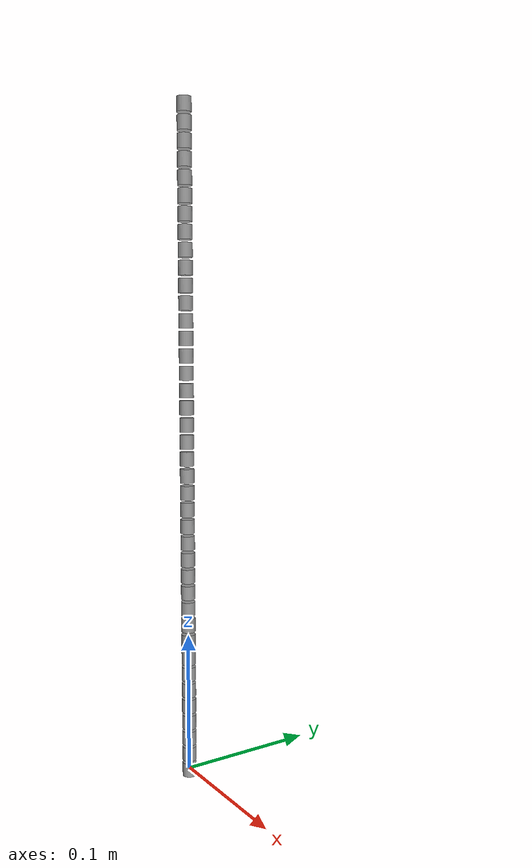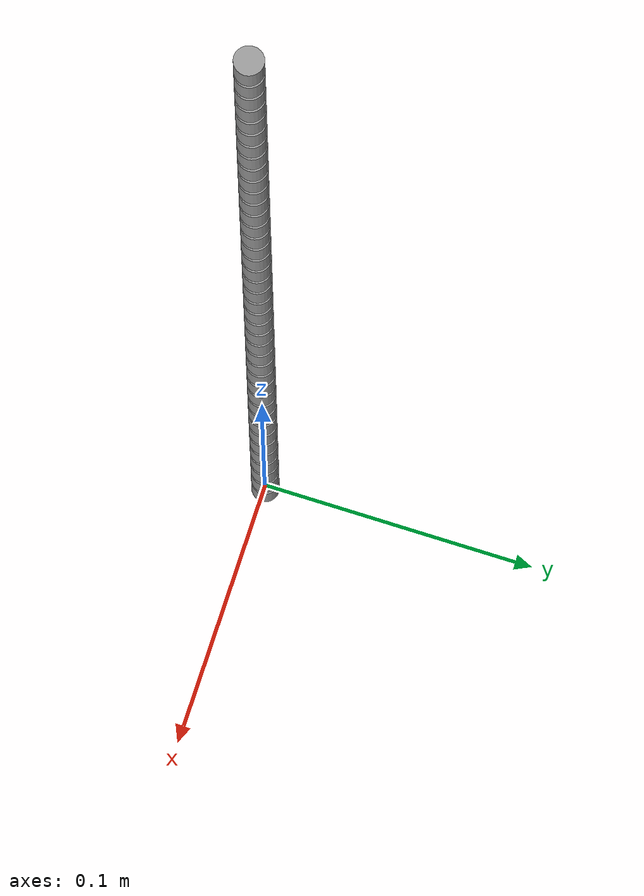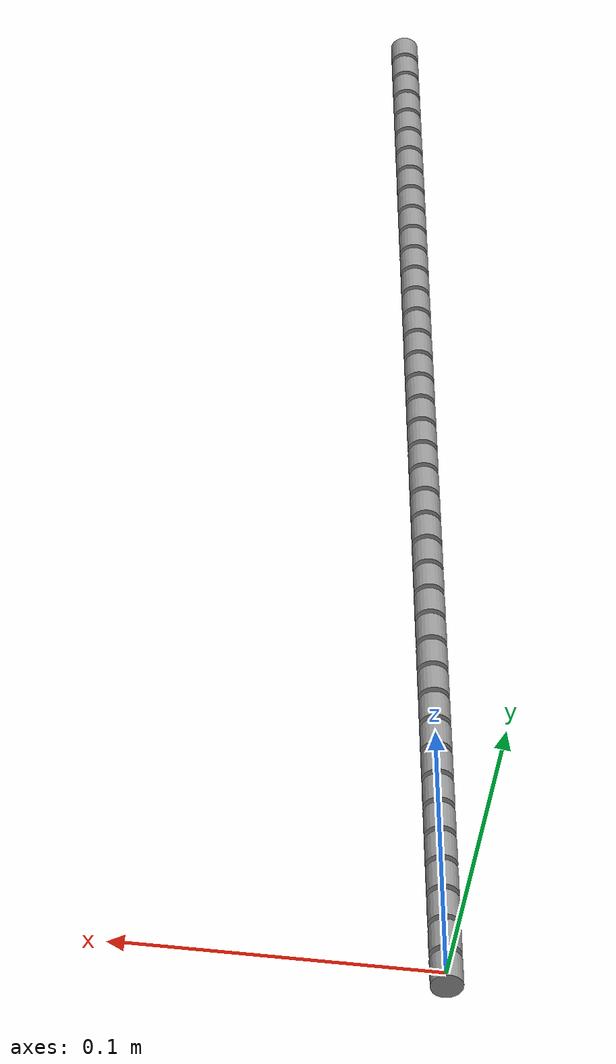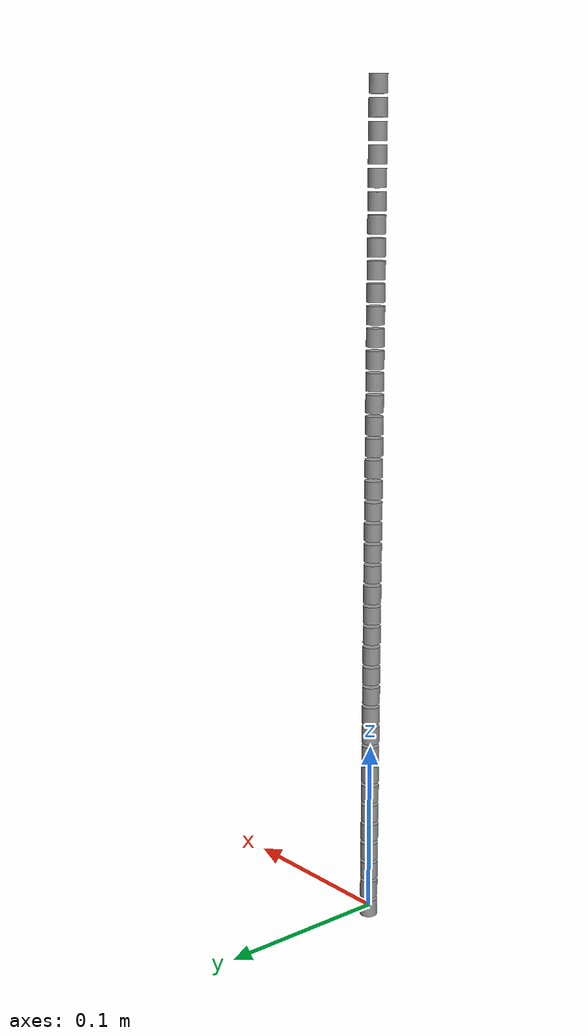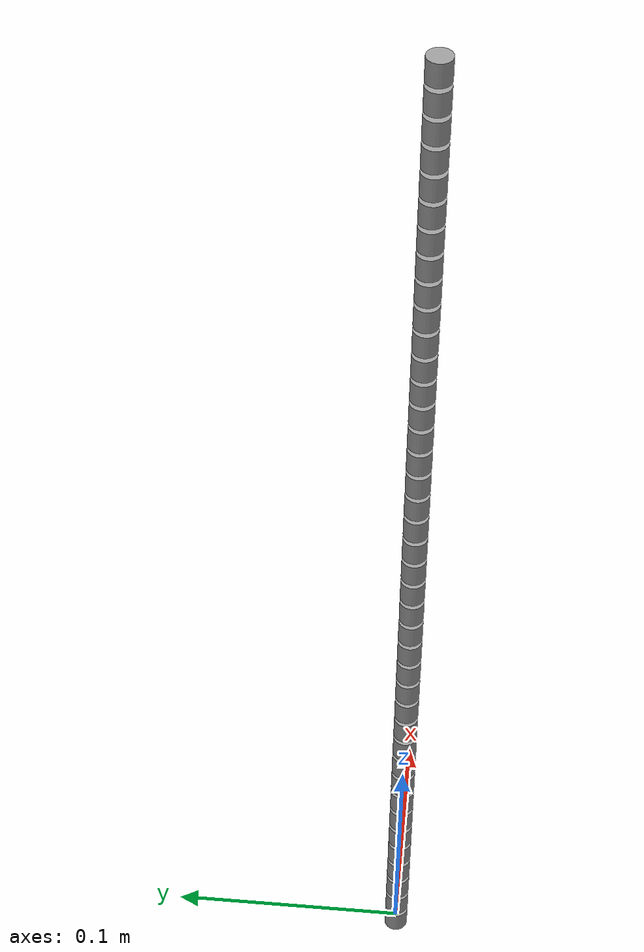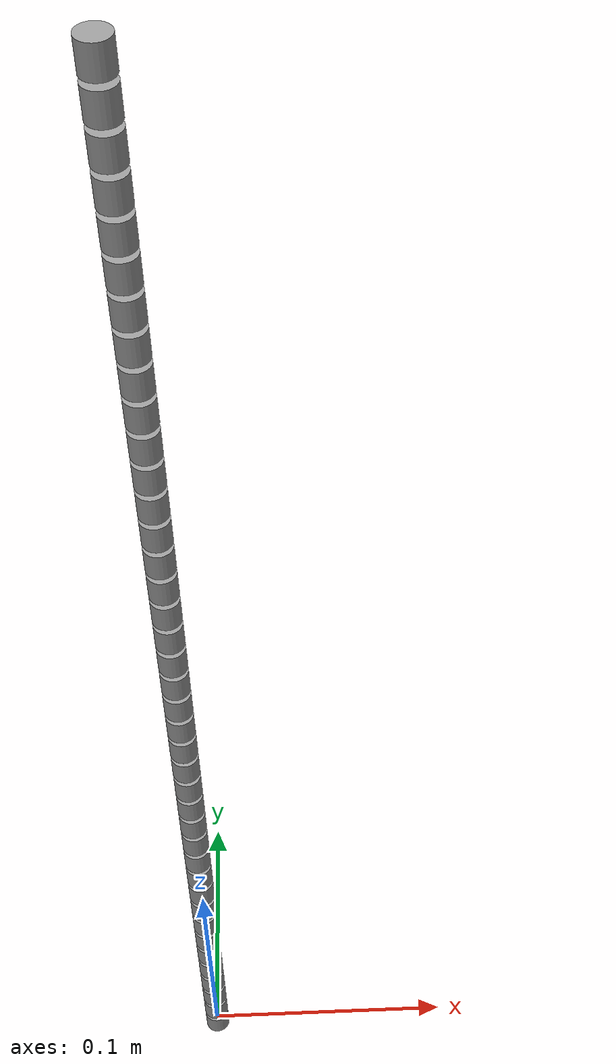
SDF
<?xml version='1.0'?>
<sdf version='1.7'>
  <model name='tether'>

    <link name='link_1'>
      <inertial>
        <mass>0.01</mass>
        <inertia>
          <ixx>1.5e-07</ixx>
          <ixy>0</ixy>
          <ixz>0</ixz>
          <iyy>1.5e-07</iyy>
          <iyz>0</iyz>
          <izz>1.3e-07</izz>
        </inertia>
        <pose>0 0 0 0 -0 0</pose>
      </inertial>
      <pose>0 0 0.0 0 -0 0</pose>
      <gravity>1</gravity>
      <self_collide>0</self_collide>
      <kinematic>0</kinematic>
      <enable_wind>0</enable_wind>
      <visual name='visual'>
        <pose>0 0 0 0 -0 0</pose>
        <geometry>
          <cylinder>
            <radius>0.005</radius>
            <length>0.01</length>
          </cylinder>
        </geometry>
        <material>
          <lighting>1</lighting>
          <script>
            <uri>file://media/materials/scripts/gazebo.material</uri>
            <name>Gazebo/Grey</name>
          </script>
          <shader type='pixel'>
            <normal_map>__default__</normal_map>
          </shader>
          <ambient>0.3 0.3 0.3 1</ambient>
          <diffuse>0.7 0.7 0.7 1</diffuse>
          <specular>0.01 0.01 0.01 1</specular>
          <emissive>0 0 0 1</emissive>
        </material>
        <transparency>0</transparency>
        <cast_shadows>1</cast_shadows>
      </visual>
      <collision name='collision'>
        <laser_retro>0</laser_retro>
        <max_contacts>10</max_contacts>
        <pose>0 0 0 0 -0 0</pose>
        <geometry>
          <cylinder>
            <radius>0.005</radius>
            <length>0.01</length>
          </cylinder>
        </geometry>
        <surface>
          <friction>
            <ode>
              <mu>1</mu>
              <mu2>1</mu2>
              <fdir1>0 0 0</fdir1>
              <slip1>0</slip1>
              <slip2>0</slip2>
            </ode>
            <torsional>
              <coefficient>1</coefficient>
              <patch_radius>0</patch_radius>
              <surface_radius>0</surface_radius>
              <use_patch_radius>1</use_patch_radius>
              <ode>
                <slip>0</slip>
              </ode>
            </torsional>
          </friction>
          <bounce>
            <restitution_coefficient>0</restitution_coefficient>
            <threshold>1e+06</threshold>
          </bounce>
          <contact>
            <collide_without_contact>0</collide_without_contact>
            <collide_without_contact_bitmask>1</collide_without_contact_bitmask>
            <collide_bitmask>1</collide_bitmask>
            <ode>
              <soft_cfm>0</soft_cfm>
              <soft_erp>0.2</soft_erp>
              <kp>1e+13</kp>
              <kd>1</kd>
              <max_vel>0.01</max_vel>
              <min_depth>0</min_depth>
            </ode>
            <bullet>
              <split_impulse>1</split_impulse>
              <split_impulse_penetration_threshold>-0.01</split_impulse_penetration_threshold>
              <soft_cfm>0</soft_cfm>
              <soft_erp>0.2</soft_erp>
              <kp>1e+13</kp>
              <kd>1</kd>
            </bullet>
          </contact>
        </surface>
      </collision>
    </link>
    <link name='link_2'>
      <inertial>
        <mass>0.01</mass>
        <inertia>
          <ixx>1.5e-07</ixx>
          <ixy>0</ixy>
          <ixz>0</ixz>
          <iyy>1.5e-07</iyy>
          <iyz>0</iyz>
          <izz>1.3e-07</izz>
        </inertia>
        <pose>0 0 0 0 -0 0</pose>
      </inertial>
      <pose>0 0 0.012 0 -0 0</pose>
      <gravity>1</gravity>
      <self_collide>0</self_collide>
      <kinematic>0</kinematic>
      <enable_wind>0</enable_wind>
      <visual name='visual'>
        <pose>0 0 0 0 -0 0</pose>
        <geometry>
          <cylinder>
            <radius>0.005</radius>
            <length>0.01</length>
          </cylinder>
        </geometry>
        <material>
          <lighting>1</lighting>
          <script>
            <uri>file://media/materials/scripts/gazebo.material</uri>
            <name>Gazebo/Grey</name>
          </script>
          <shader type='pixel'>
            <normal_map>__default__</normal_map>
          </shader>
          <ambient>0.3 0.3 0.3 1</ambient>
          <diffuse>0.7 0.7 0.7 1</diffuse>
          <specular>0.01 0.01 0.01 1</specular>
          <emissive>0 0 0 1</emissive>
        </material>
        <transparency>0</transparency>
        <cast_shadows>1</cast_shadows>
      </visual>
      <collision name='collision'>
        <laser_retro>0</laser_retro>
        <max_contacts>10</max_contacts>
        <pose>0 0 0 0 -0 0</pose>
        <geometry>
          <cylinder>
            <radius>0.005</radius>
            <length>0.01</length>
          </cylinder>
        </geometry>
        <surface>
          <friction>
            <ode>
              <mu>1</mu>
              <mu2>1</mu2>
              <fdir1>0 0 0</fdir1>
              <slip1>0</slip1>
              <slip2>0</slip2>
            </ode>
            <torsional>
              <coefficient>1</coefficient>
              <patch_radius>0</patch_radius>
              <surface_radius>0</surface_radius>
              <use_patch_radius>1</use_patch_radius>
              <ode>
                <slip>0</slip>
              </ode>
            </torsional>
          </friction>
          <bounce>
            <restitution_coefficient>0</restitution_coefficient>
            <threshold>1e+06</threshold>
          </bounce>
          <contact>
            <collide_without_contact>0</collide_without_contact>
            <collide_without_contact_bitmask>1</collide_without_contact_bitmask>
            <collide_bitmask>1</collide_bitmask>
            <ode>
              <soft_cfm>0</soft_cfm>
              <soft_erp>0.2</soft_erp>
              <kp>1e+13</kp>
              <kd>1</kd>
              <max_vel>0.01</max_vel>
              <min_depth>0</min_depth>
            </ode>
            <bullet>
              <split_impulse>1</split_impulse>
              <split_impulse_penetration_threshold>-0.01</split_impulse_penetration_threshold>
              <soft_cfm>0</soft_cfm>
              <soft_erp>0.2</soft_erp>
              <kp>1e+13</kp>
              <kd>1</kd>
            </bullet>
          </contact>
        </surface>
      </collision>
    </link>
    <link name='link_3'>
      <inertial>
        <mass>0.01</mass>
        <inertia>
          <ixx>1.5e-07</ixx>
          <ixy>0</ixy>
          <ixz>0</ixz>
          <iyy>1.5e-07</iyy>
          <iyz>0</iyz>
          <izz>1.3e-07</izz>
        </inertia>
        <pose>0 0 0 0 -0 0</pose>
      </inertial>
      <pose>0 0 0.024 0 -0 0</pose>
      <gravity>1</gravity>
      <self_collide>0</self_collide>
      <kinematic>0</kinematic>
      <enable_wind>0</enable_wind>
      <visual name='visual'>
        <pose>0 0 0 0 -0 0</pose>
        <geometry>
          <cylinder>
            <radius>0.005</radius>
            <length>0.01</length>
          </cylinder>
        </geometry>
        <material>
          <lighting>1</lighting>
          <script>
            <uri>file://media/materials/scripts/gazebo.material</uri>
            <name>Gazebo/Grey</name>
          </script>
          <shader type='pixel'>
            <normal_map>__default__</normal_map>
          </shader>
          <ambient>0.3 0.3 0.3 1</ambient>
          <diffuse>0.7 0.7 0.7 1</diffuse>
          <specular>0.01 0.01 0.01 1</specular>
          <emissive>0 0 0 1</emissive>
        </material>
        <transparency>0</transparency>
        <cast_shadows>1</cast_shadows>
      </visual>
      <collision name='collision'>
        <laser_retro>0</laser_retro>
        <max_contacts>10</max_contacts>
        <pose>0 0 0 0 -0 0</pose>
        <geometry>
          <cylinder>
            <radius>0.005</radius>
            <length>0.01</length>
          </cylinder>
        </geometry>
        <surface>
          <friction>
            <ode>
              <mu>1</mu>
              <mu2>1</mu2>
              <fdir1>0 0 0</fdir1>
              <slip1>0</slip1>
              <slip2>0</slip2>
            </ode>
            <torsional>
              <coefficient>1</coefficient>
              <patch_radius>0</patch_radius>
              <surface_radius>0</surface_radius>
              <use_patch_radius>1</use_patch_radius>
              <ode>
                <slip>0</slip>
              </ode>
            </torsional>
          </friction>
          <bounce>
            <restitution_coefficient>0</restitution_coefficient>
            <threshold>1e+06</threshold>
          </bounce>
          <contact>
            <collide_without_contact>0</collide_without_contact>
            <collide_without_contact_bitmask>1</collide_without_contact_bitmask>
            <collide_bitmask>1</collide_bitmask>
            <ode>
              <soft_cfm>0</soft_cfm>
              <soft_erp>0.2</soft_erp>
              <kp>1e+13</kp>
              <kd>1</kd>
              <max_vel>0.01</max_vel>
              <min_depth>0</min_depth>
            </ode>
            <bullet>
              <split_impulse>1</split_impulse>
              <split_impulse_penetration_threshold>-0.01</split_impulse_penetration_threshold>
              <soft_cfm>0</soft_cfm>
              <soft_erp>0.2</soft_erp>
              <kp>1e+13</kp>
              <kd>1</kd>
            </bullet>
          </contact>
        </surface>
      </collision>
    </link>
    <link name='link_4'>
      <inertial>
        <mass>0.01</mass>
        <inertia>
          <ixx>1.5e-07</ixx>
          <ixy>0</ixy>
          <ixz>0</ixz>
          <iyy>1.5e-07</iyy>
          <iyz>0</iyz>
          <izz>1.3e-07</izz>
        </inertia>
        <pose>0 0 0 0 -0 0</pose>
      </inertial>
      <pose>0 0 0.036 0 -0 0</pose>
      <gravity>1</gravity>
      <self_collide>0</self_collide>
      <kinematic>0</kinematic>
      <enable_wind>0</enable_wind>
      <visual name='visual'>
        <pose>0 0 0 0 -0 0</pose>
        <geometry>
          <cylinder>
            <radius>0.005</radius>
            <length>0.01</length>
          </cylinder>
        </geometry>
        <material>
          <lighting>1</lighting>
          <script>
            <uri>file://media/materials/scripts/gazebo.material</uri>
            <name>Gazebo/Grey</name>
          </script>
          <shader type='pixel'>
            <normal_map>__default__</normal_map>
          </shader>
          <ambient>0.3 0.3 0.3 1</ambient>
          <diffuse>0.7 0.7 0.7 1</diffuse>
          <specular>0.01 0.01 0.01 1</specular>
          <emissive>0 0 0 1</emissive>
        </material>
        <transparency>0</transparency>
        <cast_shadows>1</cast_shadows>
      </visual>
      <collision name='collision'>
        <laser_retro>0</laser_retro>
        <max_contacts>10</max_contacts>
        <pose>0 0 0 0 -0 0</pose>
        <geometry>
          <cylinder>
            <radius>0.005</radius>
            <length>0.01</length>
          </cylinder>
        </geometry>
        <surface>
          <friction>
            <ode>
              <mu>1</mu>
              <mu2>1</mu2>
              <fdir1>0 0 0</fdir1>
              <slip1>0</slip1>
              <slip2>0</slip2>
            </ode>
            <torsional>
              <coefficient>1</coefficient>
              <patch_radius>0</patch_radius>
              <surface_radius>0</surface_radius>
              <use_patch_radius>1</use_patch_radius>
              <ode>
                <slip>0</slip>
              </ode>
            </torsional>
          </friction>
          <bounce>
            <restitution_coefficient>0</restitution_coefficient>
            <threshold>1e+06</threshold>
          </bounce>
          <contact>
            <collide_without_contact>0</collide_without_contact>
            <collide_without_contact_bitmask>1</collide_without_contact_bitmask>
            <collide_bitmask>1</collide_bitmask>
            <ode>
              <soft_cfm>0</soft_cfm>
              <soft_erp>0.2</soft_erp>
              <kp>1e+13</kp>
              <kd>1</kd>
              <max_vel>0.01</max_vel>
              <min_depth>0</min_depth>
            </ode>
            <bullet>
              <split_impulse>1</split_impulse>
              <split_impulse_penetration_threshold>-0.01</split_impulse_penetration_threshold>
              <soft_cfm>0</soft_cfm>
              <soft_erp>0.2</soft_erp>
              <kp>1e+13</kp>
              <kd>1</kd>
            </bullet>
          </contact>
        </surface>
      </collision>
    </link>
    <link name='link_5'>
      <inertial>
        <mass>0.01</mass>
        <inertia>
          <ixx>1.5e-07</ixx>
          <ixy>0</ixy>
          <ixz>0</ixz>
          <iyy>1.5e-07</iyy>
          <iyz>0</iyz>
          <izz>1.3e-07</izz>
        </inertia>
        <pose>0 0 0 0 -0 0</pose>
      </inertial>
      <pose>0 0 0.048 0 -0 0</pose>
      <gravity>1</gravity>
      <self_collide>0</self_collide>
      <kinematic>0</kinematic>
      <enable_wind>0</enable_wind>
      <visual name='visual'>
        <pose>0 0 0 0 -0 0</pose>
        <geometry>
          <cylinder>
            <radius>0.005</radius>
            <length>0.01</length>
          </cylinder>
        </geometry>
        <material>
          <lighting>1</lighting>
          <script>
            <uri>file://media/materials/scripts/gazebo.material</uri>
            <name>Gazebo/Grey</name>
          </script>
          <shader type='pixel'>
            <normal_map>__default__</normal_map>
          </shader>
          <ambient>0.3 0.3 0.3 1</ambient>
          <diffuse>0.7 0.7 0.7 1</diffuse>
          <specular>0.01 0.01 0.01 1</specular>
          <emissive>0 0 0 1</emissive>
        </material>
        <transparency>0</transparency>
        <cast_shadows>1</cast_shadows>
      </visual>
      <collision name='collision'>
        <laser_retro>0</laser_retro>
        <max_contacts>10</max_contacts>
        <pose>0 0 0 0 -0 0</pose>
        <geometry>
          <cylinder>
            <radius>0.005</radius>
            <length>0.01</length>
          </cylinder>
        </geometry>
        <surface>
          <friction>
            <ode>
              <mu>1</mu>
              <mu2>1</mu2>
              <fdir1>0 0 0</fdir1>
              <slip1>0</slip1>
              <slip2>0</slip2>
            </ode>
            <torsional>
              <coefficient>1</coefficient>
              <patch_radius>0</patch_radius>
              <surface_radius>0</surface_radius>
              <use_patch_radius>1</use_patch_radius>
              <ode>
                <slip>0</slip>
              </ode>
            </torsional>
          </friction>
          <bounce>
            <restitution_coefficient>0</restitution_coefficient>
            <threshold>1e+06</threshold>
          </bounce>
          <contact>
            <collide_without_contact>0</collide_without_contact>
            <collide_without_contact_bitmask>1</collide_without_contact_bitmask>
            <collide_bitmask>1</collide_bitmask>
            <ode>
              <soft_cfm>0</soft_cfm>
              <soft_erp>0.2</soft_erp>
              <kp>1e+13</kp>
              <kd>1</kd>
              <max_vel>0.01</max_vel>
              <min_depth>0</min_depth>
            </ode>
            <bullet>
              <split_impulse>1</split_impulse>
              <split_impulse_penetration_threshold>-0.01</split_impulse_penetration_threshold>
              <soft_cfm>0</soft_cfm>
              <soft_erp>0.2</soft_erp>
              <kp>1e+13</kp>
              <kd>1</kd>
            </bullet>
          </contact>
        </surface>
      </collision>
    </link>
    <link name='link_6'>
      <inertial>
        <mass>0.01</mass>
        <inertia>
          <ixx>1.5e-07</ixx>
          <ixy>0</ixy>
          <ixz>0</ixz>
          <iyy>1.5e-07</iyy>
          <iyz>0</iyz>
          <izz>1.3e-07</izz>
        </inertia>
        <pose>0 0 0 0 -0 0</pose>
      </inertial>
      <pose>0 0 0.060 0 -0 0</pose>
      <gravity>1</gravity>
      <self_collide>0</self_collide>
      <kinematic>0</kinematic>
      <enable_wind>0</enable_wind>
      <visual name='visual'>
        <pose>0 0 0 0 -0 0</pose>
        <geometry>
          <cylinder>
            <radius>0.005</radius>
            <length>0.01</length>
          </cylinder>
        </geometry>
        <material>
          <lighting>1</lighting>
          <script>
            <uri>file://media/materials/scripts/gazebo.material</uri>
            <name>Gazebo/Grey</name>
          </script>
          <shader type='pixel'>
            <normal_map>__default__</normal_map>
          </shader>
          <ambient>0.3 0.3 0.3 1</ambient>
          <diffuse>0.7 0.7 0.7 1</diffuse>
          <specular>0.01 0.01 0.01 1</specular>
          <emissive>0 0 0 1</emissive>
        </material>
        <transparency>0</transparency>
        <cast_shadows>1</cast_shadows>
      </visual>
      <collision name='collision'>
        <laser_retro>0</laser_retro>
        <max_contacts>10</max_contacts>
        <pose>0 0 0 0 -0 0</pose>
        <geometry>
          <cylinder>
            <radius>0.005</radius>
            <length>0.01</length>
          </cylinder>
        </geometry>
        <surface>
          <friction>
            <ode>
              <mu>1</mu>
              <mu2>1</mu2>
              <fdir1>0 0 0</fdir1>
              <slip1>0</slip1>
              <slip2>0</slip2>
            </ode>
            <torsional>
              <coefficient>1</coefficient>
              <patch_radius>0</patch_radius>
              <surface_radius>0</surface_radius>
              <use_patch_radius>1</use_patch_radius>
              <ode>
                <slip>0</slip>
              </ode>
            </torsional>
          </friction>
          <bounce>
            <restitution_coefficient>0</restitution_coefficient>
            <threshold>1e+06</threshold>
          </bounce>
          <contact>
            <collide_without_contact>0</collide_without_contact>
            <collide_without_contact_bitmask>1</collide_without_contact_bitmask>
            <collide_bitmask>1</collide_bitmask>
            <ode>
              <soft_cfm>0</soft_cfm>
              <soft_erp>0.2</soft_erp>
              <kp>1e+13</kp>
              <kd>1</kd>
              <max_vel>0.01</max_vel>
              <min_depth>0</min_depth>
            </ode>
            <bullet>
              <split_impulse>1</split_impulse>
              <split_impulse_penetration_threshold>-0.01</split_impulse_penetration_threshold>
              <soft_cfm>0</soft_cfm>
              <soft_erp>0.2</soft_erp>
              <kp>1e+13</kp>
              <kd>1</kd>
            </bullet>
          </contact>
        </surface>
      </collision>
    </link>
    <link name='link_7'>
      <inertial>
        <mass>0.01</mass>
        <inertia>
          <ixx>1.5e-07</ixx>
          <ixy>0</ixy>
          <ixz>0</ixz>
          <iyy>1.5e-07</iyy>
          <iyz>0</iyz>
          <izz>1.3e-07</izz>
        </inertia>
        <pose>0 0 0 0 -0 0</pose>
      </inertial>
      <pose>0 0 0.072 0 -0 0</pose>
      <gravity>1</gravity>
      <self_collide>0</self_collide>
      <kinematic>0</kinematic>
      <enable_wind>0</enable_wind>
      <visual name='visual'>
        <pose>0 0 0 0 -0 0</pose>
        <geometry>
          <cylinder>
            <radius>0.005</radius>
            <length>0.01</length>
          </cylinder>
        </geometry>
        <material>
          <lighting>1</lighting>
          <script>
            <uri>file://media/materials/scripts/gazebo.material</uri>
            <name>Gazebo/Grey</name>
          </script>
          <shader type='pixel'>
            <normal_map>__default__</normal_map>
          </shader>
          <ambient>0.3 0.3 0.3 1</ambient>
          <diffuse>0.7 0.7 0.7 1</diffuse>
          <specular>0.01 0.01 0.01 1</specular>
          <emissive>0 0 0 1</emissive>
        </material>
        <transparency>0</transparency>
        <cast_shadows>1</cast_shadows>
      </visual>
      <collision name='collision'>
        <laser_retro>0</laser_retro>
        <max_contacts>10</max_contacts>
        <pose>0 0 0 0 -0 0</pose>
        <geometry>
          <cylinder>
            <radius>0.005</radius>
            <length>0.01</length>
          </cylinder>
        </geometry>
        <surface>
          <friction>
            <ode>
              <mu>1</mu>
              <mu2>1</mu2>
              <fdir1>0 0 0</fdir1>
              <slip1>0</slip1>
              <slip2>0</slip2>
            </ode>
            <torsional>
              <coefficient>1</coefficient>
              <patch_radius>0</patch_radius>
              <surface_radius>0</surface_radius>
              <use_patch_radius>1</use_patch_radius>
              <ode>
                <slip>0</slip>
              </ode>
            </torsional>
          </friction>
          <bounce>
            <restitution_coefficient>0</restitution_coefficient>
            <threshold>1e+06</threshold>
          </bounce>
          <contact>
            <collide_without_contact>0</collide_without_contact>
            <collide_without_contact_bitmask>1</collide_without_contact_bitmask>
            <collide_bitmask>1</collide_bitmask>
            <ode>
              <soft_cfm>0</soft_cfm>
              <soft_erp>0.2</soft_erp>
              <kp>1e+13</kp>
              <kd>1</kd>
              <max_vel>0.01</max_vel>
              <min_depth>0</min_depth>
            </ode>
            <bullet>
              <split_impulse>1</split_impulse>
              <split_impulse_penetration_threshold>-0.01</split_impulse_penetration_threshold>
              <soft_cfm>0</soft_cfm>
              <soft_erp>0.2</soft_erp>
              <kp>1e+13</kp>
              <kd>1</kd>
            </bullet>
          </contact>
        </surface>
      </collision>
    </link>
    <link name='link_8'>
      <inertial>
        <mass>0.01</mass>
        <inertia>
          <ixx>1.5e-07</ixx>
          <ixy>0</ixy>
          <ixz>0</ixz>
          <iyy>1.5e-07</iyy>
          <iyz>0</iyz>
          <izz>1.3e-07</izz>
        </inertia>
        <pose>0 0 0 0 -0 0</pose>
      </inertial>
      <pose>0 0 0.084 0 -0 0</pose>
      <gravity>1</gravity>
      <self_collide>0</self_collide>
      <kinematic>0</kinematic>
      <enable_wind>0</enable_wind>
      <visual name='visual'>
        <pose>0 0 0 0 -0 0</pose>
        <geometry>
          <cylinder>
            <radius>0.005</radius>
            <length>0.01</length>
          </cylinder>
        </geometry>
        <material>
          <lighting>1</lighting>
          <script>
            <uri>file://media/materials/scripts/gazebo.material</uri>
            <name>Gazebo/Grey</name>
          </script>
          <shader type='pixel'>
            <normal_map>__default__</normal_map>
          </shader>
          <ambient>0.3 0.3 0.3 1</ambient>
          <diffuse>0.7 0.7 0.7 1</diffuse>
          <specular>0.01 0.01 0.01 1</specular>
          <emissive>0 0 0 1</emissive>
        </material>
        <transparency>0</transparency>
        <cast_shadows>1</cast_shadows>
      </visual>
      <collision name='collision'>
        <laser_retro>0</laser_retro>
        <max_contacts>10</max_contacts>
        <pose>0 0 0 0 -0 0</pose>
        <geometry>
          <cylinder>
            <radius>0.005</radius>
            <length>0.01</length>
          </cylinder>
        </geometry>
        <surface>
          <friction>
            <ode>
              <mu>1</mu>
              <mu2>1</mu2>
              <fdir1>0 0 0</fdir1>
              <slip1>0</slip1>
              <slip2>0</slip2>
            </ode>
            <torsional>
              <coefficient>1</coefficient>
              <patch_radius>0</patch_radius>
              <surface_radius>0</surface_radius>
              <use_patch_radius>1</use_patch_radius>
              <ode>
                <slip>0</slip>
              </ode>
            </torsional>
          </friction>
          <bounce>
            <restitution_coefficient>0</restitution_coefficient>
            <threshold>1e+06</threshold>
          </bounce>
          <contact>
            <collide_without_contact>0</collide_without_contact>
            <collide_without_contact_bitmask>1</collide_without_contact_bitmask>
            <collide_bitmask>1</collide_bitmask>
            <ode>
              <soft_cfm>0</soft_cfm>
              <soft_erp>0.2</soft_erp>
              <kp>1e+13</kp>
              <kd>1</kd>
              <max_vel>0.01</max_vel>
              <min_depth>0</min_depth>
            </ode>
            <bullet>
              <split_impulse>1</split_impulse>
              <split_impulse_penetration_threshold>-0.01</split_impulse_penetration_threshold>
              <soft_cfm>0</soft_cfm>
              <soft_erp>0.2</soft_erp>
              <kp>1e+13</kp>
              <kd>1</kd>
            </bullet>
          </contact>
        </surface>
      </collision>
    </link>
    <link name='link_9'>
      <inertial>
        <mass>0.01</mass>
        <inertia>
          <ixx>1.5e-07</ixx>
          <ixy>0</ixy>
          <ixz>0</ixz>
          <iyy>1.5e-07</iyy>
          <iyz>0</iyz>
          <izz>1.3e-07</izz>
        </inertia>
        <pose>0 0 0 0 -0 0</pose>
      </inertial>
      <pose>0 0 0.096 0 -0 0</pose>
      <gravity>1</gravity>
      <self_collide>0</self_collide>
      <kinematic>0</kinematic>
      <enable_wind>0</enable_wind>
      <visual name='visual'>
        <pose>0 0 0 0 -0 0</pose>
        <geometry>
          <cylinder>
            <radius>0.005</radius>
            <length>0.01</length>
          </cylinder>
        </geometry>
        <material>
          <lighting>1</lighting>
          <script>
            <uri>file://media/materials/scripts/gazebo.material</uri>
            <name>Gazebo/Grey</name>
          </script>
          <shader type='pixel'>
            <normal_map>__default__</normal_map>
          </shader>
          <ambient>0.3 0.3 0.3 1</ambient>
          <diffuse>0.7 0.7 0.7 1</diffuse>
          <specular>0.01 0.01 0.01 1</specular>
          <emissive>0 0 0 1</emissive>
        </material>
        <transparency>0</transparency>
        <cast_shadows>1</cast_shadows>
      </visual>
      <collision name='collision'>
        <laser_retro>0</laser_retro>
        <max_contacts>10</max_contacts>
        <pose>0 0 0 0 -0 0</pose>
        <geometry>
          <cylinder>
            <radius>0.005</radius>
            <length>0.01</length>
          </cylinder>
        </geometry>
        <surface>
          <friction>
            <ode>
              <mu>1</mu>
              <mu2>1</mu2>
              <fdir1>0 0 0</fdir1>
              <slip1>0</slip1>
              <slip2>0</slip2>
            </ode>
            <torsional>
              <coefficient>1</coefficient>
              <patch_radius>0</patch_radius>
              <surface_radius>0</surface_radius>
              <use_patch_radius>1</use_patch_radius>
              <ode>
                <slip>0</slip>
              </ode>
            </torsional>
          </friction>
          <bounce>
            <restitution_coefficient>0</restitution_coefficient>
            <threshold>1e+06</threshold>
          </bounce>
          <contact>
            <collide_without_contact>0</collide_without_contact>
            <collide_without_contact_bitmask>1</collide_without_contact_bitmask>
            <collide_bitmask>1</collide_bitmask>
            <ode>
              <soft_cfm>0</soft_cfm>
              <soft_erp>0.2</soft_erp>
              <kp>1e+13</kp>
              <kd>1</kd>
              <max_vel>0.01</max_vel>
              <min_depth>0</min_depth>
            </ode>
            <bullet>
              <split_impulse>1</split_impulse>
              <split_impulse_penetration_threshold>-0.01</split_impulse_penetration_threshold>
              <soft_cfm>0</soft_cfm>
              <soft_erp>0.2</soft_erp>
              <kp>1e+13</kp>
              <kd>1</kd>
            </bullet>
          </contact>
        </surface>
      </collision>
    </link>
    <link name='link_10'>
      <inertial>
        <mass>0.01</mass>
        <inertia>
          <ixx>1.5e-07</ixx>
          <ixy>0</ixy>
          <ixz>0</ixz>
          <iyy>1.5e-07</iyy>
          <iyz>0</iyz>
          <izz>1.3e-07</izz>
        </inertia>
        <pose>0 0 0 0 -0 0</pose>
      </inertial>
      <pose>0 0 0.108 0 -0 0</pose>
      <gravity>1</gravity>
      <self_collide>0</self_collide>
      <kinematic>0</kinematic>
      <enable_wind>0</enable_wind>
      <visual name='visual'>
        <pose>0 0 0 0 -0 0</pose>
        <geometry>
          <cylinder>
            <radius>0.005</radius>
            <length>0.01</length>
          </cylinder>
        </geometry>
        <material>
          <lighting>1</lighting>
          <script>
            <uri>file://media/materials/scripts/gazebo.material</uri>
            <name>Gazebo/Grey</name>
          </script>
          <shader type='pixel'>
            <normal_map>__default__</normal_map>
          </shader>
          <ambient>0.3 0.3 0.3 1</ambient>
          <diffuse>0.7 0.7 0.7 1</diffuse>
          <specular>0.01 0.01 0.01 1</specular>
          <emissive>0 0 0 1</emissive>
        </material>
        <transparency>0</transparency>
        <cast_shadows>1</cast_shadows>
      </visual>
      <collision name='collision'>
        <laser_retro>0</laser_retro>
        <max_contacts>10</max_contacts>
        <pose>0 0 0 0 -0 0</pose>
        <geometry>
          <cylinder>
            <radius>0.005</radius>
            <length>0.01</length>
          </cylinder>
        </geometry>
        <surface>
          <friction>
            <ode>
              <mu>1</mu>
              <mu2>1</mu2>
              <fdir1>0 0 0</fdir1>
              <slip1>0</slip1>
              <slip2>0</slip2>
            </ode>
            <torsional>
              <coefficient>1</coefficient>
              <patch_radius>0</patch_radius>
              <surface_radius>0</surface_radius>
              <use_patch_radius>1</use_patch_radius>
              <ode>
                <slip>0</slip>
              </ode>
            </torsional>
          </friction>
          <bounce>
            <restitution_coefficient>0</restitution_coefficient>
            <threshold>1e+06</threshold>
          </bounce>
          <contact>
            <collide_without_contact>0</collide_without_contact>
            <collide_without_contact_bitmask>1</collide_without_contact_bitmask>
            <collide_bitmask>1</collide_bitmask>
            <ode>
              <soft_cfm>0</soft_cfm>
              <soft_erp>0.2</soft_erp>
              <kp>1e+13</kp>
              <kd>1</kd>
              <max_vel>0.01</max_vel>
              <min_depth>0</min_depth>
            </ode>
            <bullet>
              <split_impulse>1</split_impulse>
              <split_impulse_penetration_threshold>-0.01</split_impulse_penetration_threshold>
              <soft_cfm>0</soft_cfm>
              <soft_erp>0.2</soft_erp>
              <kp>1e+13</kp>
              <kd>1</kd>
            </bullet>
          </contact>
        </surface>
      </collision>
    </link>
    <link name='link_11'>
      <inertial>
        <mass>0.01</mass>
        <inertia>
          <ixx>1.5e-07</ixx>
          <ixy>0</ixy>
          <ixz>0</ixz>
          <iyy>1.5e-07</iyy>
          <iyz>0</iyz>
          <izz>1.3e-07</izz>
        </inertia>
        <pose>0 0 0 0 -0 0</pose>
      </inertial>
      <pose>0 0 0.120 0 -0 0</pose>
      <gravity>1</gravity>
      <self_collide>0</self_collide>
      <kinematic>0</kinematic>
      <enable_wind>0</enable_wind>
      <visual name='visual'>
        <pose>0 0 0 0 -0 0</pose>
        <geometry>
          <cylinder>
            <radius>0.005</radius>
            <length>0.01</length>
          </cylinder>
        </geometry>
        <material>
          <lighting>1</lighting>
          <script>
            <uri>file://media/materials/scripts/gazebo.material</uri>
            <name>Gazebo/Grey</name>
          </script>
          <shader type='pixel'>
            <normal_map>__default__</normal_map>
          </shader>
          <ambient>0.3 0.3 0.3 1</ambient>
          <diffuse>0.7 0.7 0.7 1</diffuse>
          <specular>0.01 0.01 0.01 1</specular>
          <emissive>0 0 0 1</emissive>
        </material>
        <transparency>0</transparency>
        <cast_shadows>1</cast_shadows>
      </visual>
      <collision name='collision'>
        <laser_retro>0</laser_retro>
        <max_contacts>10</max_contacts>
        <pose>0 0 0 0 -0 0</pose>
        <geometry>
          <cylinder>
            <radius>0.005</radius>
            <length>0.01</length>
          </cylinder>
        </geometry>
        <surface>
          <friction>
            <ode>
              <mu>1</mu>
              <mu2>1</mu2>
              <fdir1>0 0 0</fdir1>
              <slip1>0</slip1>
              <slip2>0</slip2>
            </ode>
            <torsional>
              <coefficient>1</coefficient>
              <patch_radius>0</patch_radius>
              <surface_radius>0</surface_radius>
              <use_patch_radius>1</use_patch_radius>
              <ode>
                <slip>0</slip>
              </ode>
            </torsional>
          </friction>
          <bounce>
            <restitution_coefficient>0</restitution_coefficient>
            <threshold>1e+06</threshold>
          </bounce>
          <contact>
            <collide_without_contact>0</collide_without_contact>
            <collide_without_contact_bitmask>1</collide_without_contact_bitmask>
            <collide_bitmask>1</collide_bitmask>
            <ode>
              <soft_cfm>0</soft_cfm>
              <soft_erp>0.2</soft_erp>
              <kp>1e+13</kp>
              <kd>1</kd>
              <max_vel>0.01</max_vel>
              <min_depth>0</min_depth>
            </ode>
            <bullet>
              <split_impulse>1</split_impulse>
              <split_impulse_penetration_threshold>-0.01</split_impulse_penetration_threshold>
              <soft_cfm>0</soft_cfm>
              <soft_erp>0.2</soft_erp>
              <kp>1e+13</kp>
              <kd>1</kd>
            </bullet>
          </contact>
        </surface>
      </collision>
    </link>
    <link name='link_12'>
      <inertial>
        <mass>0.01</mass>
        <inertia>
          <ixx>1.5e-07</ixx>
          <ixy>0</ixy>
          <ixz>0</ixz>
          <iyy>1.5e-07</iyy>
          <iyz>0</iyz>
          <izz>1.3e-07</izz>
        </inertia>
        <pose>0 0 0 0 -0 0</pose>
      </inertial>
      <pose>0 0 0.132 0 -0 0</pose>
      <gravity>1</gravity>
      <self_collide>0</self_collide>
      <kinematic>0</kinematic>
      <enable_wind>0</enable_wind>
      <visual name='visual'>
        <pose>0 0 0 0 -0 0</pose>
        <geometry>
          <cylinder>
            <radius>0.005</radius>
            <length>0.01</length>
          </cylinder>
        </geometry>
        <material>
          <lighting>1</lighting>
          <script>
            <uri>file://media/materials/scripts/gazebo.material</uri>
            <name>Gazebo/Grey</name>
          </script>
          <shader type='pixel'>
            <normal_map>__default__</normal_map>
          </shader>
          <ambient>0.3 0.3 0.3 1</ambient>
          <diffuse>0.7 0.7 0.7 1</diffuse>
          <specular>0.01 0.01 0.01 1</specular>
          <emissive>0 0 0 1</emissive>
        </material>
        <transparency>0</transparency>
        <cast_shadows>1</cast_shadows>
      </visual>
      <collision name='collision'>
        <laser_retro>0</laser_retro>
        <max_contacts>10</max_contacts>
        <pose>0 0 0 0 -0 0</pose>
        <geometry>
          <cylinder>
            <radius>0.005</radius>
            <length>0.01</length>
          </cylinder>
        </geometry>
        <surface>
          <friction>
            <ode>
              <mu>1</mu>
              <mu2>1</mu2>
              <fdir1>0 0 0</fdir1>
              <slip1>0</slip1>
              <slip2>0</slip2>
            </ode>
            <torsional>
              <coefficient>1</coefficient>
              <patch_radius>0</patch_radius>
              <surface_radius>0</surface_radius>
              <use_patch_radius>1</use_patch_radius>
              <ode>
                <slip>0</slip>
              </ode>
            </torsional>
          </friction>
          <bounce>
            <restitution_coefficient>0</restitution_coefficient>
            <threshold>1e+06</threshold>
          </bounce>
          <contact>
            <collide_without_contact>0</collide_without_contact>
            <collide_without_contact_bitmask>1</collide_without_contact_bitmask>
            <collide_bitmask>1</collide_bitmask>
            <ode>
              <soft_cfm>0</soft_cfm>
              <soft_erp>0.2</soft_erp>
              <kp>1e+13</kp>
              <kd>1</kd>
              <max_vel>0.01</max_vel>
              <min_depth>0</min_depth>
            </ode>
            <bullet>
              <split_impulse>1</split_impulse>
              <split_impulse_penetration_threshold>-0.01</split_impulse_penetration_threshold>
              <soft_cfm>0</soft_cfm>
              <soft_erp>0.2</soft_erp>
              <kp>1e+13</kp>
              <kd>1</kd>
            </bullet>
          </contact>
        </surface>
      </collision>
    </link>
    <link name='link_13'>
      <inertial>
        <mass>0.01</mass>
        <inertia>
          <ixx>1.5e-07</ixx>
          <ixy>0</ixy>
          <ixz>0</ixz>
          <iyy>1.5e-07</iyy>
          <iyz>0</iyz>
          <izz>1.3e-07</izz>
        </inertia>
        <pose>0 0 0 0 -0 0</pose>
      </inertial>
      <pose>0 0 0.144 0 -0 0</pose>
      <gravity>1</gravity>
      <self_collide>0</self_collide>
      <kinematic>0</kinematic>
      <enable_wind>0</enable_wind>
      <visual name='visual'>
        <pose>0 0 0 0 -0 0</pose>
        <geometry>
          <cylinder>
            <radius>0.005</radius>
            <length>0.01</length>
          </cylinder>
        </geometry>
        <material>
          <lighting>1</lighting>
          <script>
            <uri>file://media/materials/scripts/gazebo.material</uri>
            <name>Gazebo/Grey</name>
          </script>
          <shader type='pixel'>
            <normal_map>__default__</normal_map>
          </shader>
          <ambient>0.3 0.3 0.3 1</ambient>
          <diffuse>0.7 0.7 0.7 1</diffuse>
          <specular>0.01 0.01 0.01 1</specular>
          <emissive>0 0 0 1</emissive>
        </material>
        <transparency>0</transparency>
        <cast_shadows>1</cast_shadows>
      </visual>
      <collision name='collision'>
        <laser_retro>0</laser_retro>
        <max_contacts>10</max_contacts>
        <pose>0 0 0 0 -0 0</pose>
        <geometry>
          <cylinder>
            <radius>0.005</radius>
            <length>0.01</length>
          </cylinder>
        </geometry>
        <surface>
          <friction>
            <ode>
              <mu>1</mu>
              <mu2>1</mu2>
              <fdir1>0 0 0</fdir1>
              <slip1>0</slip1>
              <slip2>0</slip2>
            </ode>
            <torsional>
              <coefficient>1</coefficient>
              <patch_radius>0</patch_radius>
              <surface_radius>0</surface_radius>
              <use_patch_radius>1</use_patch_radius>
              <ode>
                <slip>0</slip>
              </ode>
            </torsional>
          </friction>
          <bounce>
            <restitution_coefficient>0</restitution_coefficient>
            <threshold>1e+06</threshold>
          </bounce>
          <contact>
            <collide_without_contact>0</collide_without_contact>
            <collide_without_contact_bitmask>1</collide_without_contact_bitmask>
            <collide_bitmask>1</collide_bitmask>
            <ode>
              <soft_cfm>0</soft_cfm>
              <soft_erp>0.2</soft_erp>
              <kp>1e+13</kp>
              <kd>1</kd>
              <max_vel>0.01</max_vel>
              <min_depth>0</min_depth>
            </ode>
            <bullet>
              <split_impulse>1</split_impulse>
              <split_impulse_penetration_threshold>-0.01</split_impulse_penetration_threshold>
              <soft_cfm>0</soft_cfm>
              <soft_erp>0.2</soft_erp>
              <kp>1e+13</kp>
              <kd>1</kd>
            </bullet>
          </contact>
        </surface>
      </collision>
    </link>
    <link name='link_14'>
      <inertial>
        <mass>0.01</mass>
        <inertia>
          <ixx>1.5e-07</ixx>
          <ixy>0</ixy>
          <ixz>0</ixz>
          <iyy>1.5e-07</iyy>
          <iyz>0</iyz>
          <izz>1.3e-07</izz>
        </inertia>
        <pose>0 0 0 0 -0 0</pose>
      </inertial>
      <pose>0 0 0.156 0 -0 0</pose>
      <gravity>1</gravity>
      <self_collide>0</self_collide>
      <kinematic>0</kinematic>
      <enable_wind>0</enable_wind>
      <visual name='visual'>
        <pose>0 0 0 0 -0 0</pose>
        <geometry>
          <cylinder>
            <radius>0.005</radius>
            <length>0.01</length>
          </cylinder>
        </geometry>
        <material>
          <lighting>1</lighting>
          <script>
            <uri>file://media/materials/scripts/gazebo.material</uri>
            <name>Gazebo/Grey</name>
          </script>
          <shader type='pixel'>
            <normal_map>__default__</normal_map>
          </shader>
          <ambient>0.3 0.3 0.3 1</ambient>
          <diffuse>0.7 0.7 0.7 1</diffuse>
          <specular>0.01 0.01 0.01 1</specular>
          <emissive>0 0 0 1</emissive>
        </material>
        <transparency>0</transparency>
        <cast_shadows>1</cast_shadows>
      </visual>
      <collision name='collision'>
        <laser_retro>0</laser_retro>
        <max_contacts>10</max_contacts>
        <pose>0 0 0 0 -0 0</pose>
        <geometry>
          <cylinder>
            <radius>0.005</radius>
            <length>0.01</length>
          </cylinder>
        </geometry>
        <surface>
          <friction>
            <ode>
              <mu>1</mu>
              <mu2>1</mu2>
              <fdir1>0 0 0</fdir1>
              <slip1>0</slip1>
              <slip2>0</slip2>
            </ode>
            <torsional>
              <coefficient>1</coefficient>
              <patch_radius>0</patch_radius>
              <surface_radius>0</surface_radius>
              <use_patch_radius>1</use_patch_radius>
              <ode>
                <slip>0</slip>
              </ode>
            </torsional>
          </friction>
          <bounce>
            <restitution_coefficient>0</restitution_coefficient>
            <threshold>1e+06</threshold>
          </bounce>
          <contact>
            <collide_without_contact>0</collide_without_contact>
            <collide_without_contact_bitmask>1</collide_without_contact_bitmask>
            <collide_bitmask>1</collide_bitmask>
            <ode>
              <soft_cfm>0</soft_cfm>
              <soft_erp>0.2</soft_erp>
              <kp>1e+13</kp>
              <kd>1</kd>
              <max_vel>0.01</max_vel>
              <min_depth>0</min_depth>
            </ode>
            <bullet>
              <split_impulse>1</split_impulse>
              <split_impulse_penetration_threshold>-0.01</split_impulse_penetration_threshold>
              <soft_cfm>0</soft_cfm>
              <soft_erp>0.2</soft_erp>
              <kp>1e+13</kp>
              <kd>1</kd>
            </bullet>
          </contact>
        </surface>
      </collision>
    </link>
    <link name='link_15'>
      <inertial>
        <mass>0.01</mass>
        <inertia>
          <ixx>1.5e-07</ixx>
          <ixy>0</ixy>
          <ixz>0</ixz>
          <iyy>1.5e-07</iyy>
          <iyz>0</iyz>
          <izz>1.3e-07</izz>
        </inertia>
        <pose>0 0 0 0 -0 0</pose>
      </inertial>
      <pose>0 0 0.168 0 -0 0</pose>
      <gravity>1</gravity>
      <self_collide>0</self_collide>
      <kinematic>0</kinematic>
      <enable_wind>0</enable_wind>
      <visual name='visual'>
        <pose>0 0 0 0 -0 0</pose>
        <geometry>
          <cylinder>
            <radius>0.005</radius>
            <length>0.01</length>
          </cylinder>
        </geometry>
        <material>
          <lighting>1</lighting>
          <script>
            <uri>file://media/materials/scripts/gazebo.material</uri>
            <name>Gazebo/Grey</name>
          </script>
          <shader type='pixel'>
            <normal_map>__default__</normal_map>
          </shader>
          <ambient>0.3 0.3 0.3 1</ambient>
          <diffuse>0.7 0.7 0.7 1</diffuse>
          <specular>0.01 0.01 0.01 1</specular>
          <emissive>0 0 0 1</emissive>
        </material>
        <transparency>0</transparency>
        <cast_shadows>1</cast_shadows>
      </visual>
      <collision name='collision'>
        <laser_retro>0</laser_retro>
        <max_contacts>10</max_contacts>
        <pose>0 0 0 0 -0 0</pose>
        <geometry>
          <cylinder>
            <radius>0.005</radius>
            <length>0.01</length>
          </cylinder>
        </geometry>
        <surface>
          <friction>
            <ode>
              <mu>1</mu>
              <mu2>1</mu2>
              <fdir1>0 0 0</fdir1>
              <slip1>0</slip1>
              <slip2>0</slip2>
            </ode>
            <torsional>
              <coefficient>1</coefficient>
              <patch_radius>0</patch_radius>
              <surface_radius>0</surface_radius>
              <use_patch_radius>1</use_patch_radius>
              <ode>
                <slip>0</slip>
              </ode>
            </torsional>
          </friction>
          <bounce>
            <restitution_coefficient>0</restitution_coefficient>
            <threshold>1e+06</threshold>
          </bounce>
          <contact>
            <collide_without_contact>0</collide_without_contact>
            <collide_without_contact_bitmask>1</collide_without_contact_bitmask>
            <collide_bitmask>1</collide_bitmask>
            <ode>
              <soft_cfm>0</soft_cfm>
              <soft_erp>0.2</soft_erp>
              <kp>1e+13</kp>
              <kd>1</kd>
              <max_vel>0.01</max_vel>
              <min_depth>0</min_depth>
            </ode>
            <bullet>
              <split_impulse>1</split_impulse>
              <split_impulse_penetration_threshold>-0.01</split_impulse_penetration_threshold>
              <soft_cfm>0</soft_cfm>
              <soft_erp>0.2</soft_erp>
              <kp>1e+13</kp>
              <kd>1</kd>
            </bullet>
          </contact>
        </surface>
      </collision>
    </link>
    <link name='link_16'>
      <inertial>
        <mass>0.01</mass>
        <inertia>
          <ixx>1.5e-07</ixx>
          <ixy>0</ixy>
          <ixz>0</ixz>
          <iyy>1.5e-07</iyy>
          <iyz>0</iyz>
          <izz>1.3e-07</izz>
        </inertia>
        <pose>0 0 0 0 -0 0</pose>
      </inertial>
      <pose>0 0 0.180 0 -0 0</pose>
      <gravity>1</gravity>
      <self_collide>0</self_collide>
      <kinematic>0</kinematic>
      <enable_wind>0</enable_wind>
      <visual name='visual'>
        <pose>0 0 0 0 -0 0</pose>
        <geometry>
          <cylinder>
            <radius>0.005</radius>
            <length>0.01</length>
          </cylinder>
        </geometry>
        <material>
          <lighting>1</lighting>
          <script>
            <uri>file://media/materials/scripts/gazebo.material</uri>
            <name>Gazebo/Grey</name>
          </script>
          <shader type='pixel'>
            <normal_map>__default__</normal_map>
          </shader>
          <ambient>0.3 0.3 0.3 1</ambient>
          <diffuse>0.7 0.7 0.7 1</diffuse>
          <specular>0.01 0.01 0.01 1</specular>
          <emissive>0 0 0 1</emissive>
        </material>
        <transparency>0</transparency>
        <cast_shadows>1</cast_shadows>
      </visual>
      <collision name='collision'>
        <laser_retro>0</laser_retro>
        <max_contacts>10</max_contacts>
        <pose>0 0 0 0 -0 0</pose>
        <geometry>
          <cylinder>
            <radius>0.005</radius>
            <length>0.01</length>
          </cylinder>
        </geometry>
        <surface>
          <friction>
            <ode>
              <mu>1</mu>
              <mu2>1</mu2>
              <fdir1>0 0 0</fdir1>
              <slip1>0</slip1>
              <slip2>0</slip2>
            </ode>
            <torsional>
              <coefficient>1</coefficient>
              <patch_radius>0</patch_radius>
              <surface_radius>0</surface_radius>
              <use_patch_radius>1</use_patch_radius>
              <ode>
                <slip>0</slip>
              </ode>
            </torsional>
          </friction>
          <bounce>
            <restitution_coefficient>0</restitution_coefficient>
            <threshold>1e+06</threshold>
          </bounce>
          <contact>
            <collide_without_contact>0</collide_without_contact>
            <collide_without_contact_bitmask>1</collide_without_contact_bitmask>
            <collide_bitmask>1</collide_bitmask>
            <ode>
              <soft_cfm>0</soft_cfm>
              <soft_erp>0.2</soft_erp>
              <kp>1e+13</kp>
              <kd>1</kd>
              <max_vel>0.01</max_vel>
              <min_depth>0</min_depth>
            </ode>
            <bullet>
              <split_impulse>1</split_impulse>
              <split_impulse_penetration_threshold>-0.01</split_impulse_penetration_threshold>
              <soft_cfm>0</soft_cfm>
              <soft_erp>0.2</soft_erp>
              <kp>1e+13</kp>
              <kd>1</kd>
            </bullet>
          </contact>
        </surface>
      </collision>
    </link>
    <link name='link_17'>
      <inertial>
        <mass>0.01</mass>
        <inertia>
          <ixx>1.5e-07</ixx>
          <ixy>0</ixy>
          <ixz>0</ixz>
          <iyy>1.5e-07</iyy>
          <iyz>0</iyz>
          <izz>1.3e-07</izz>
        </inertia>
        <pose>0 0 0 0 -0 0</pose>
      </inertial>
      <pose>0 0 0.192 0 -0 0</pose>
      <gravity>1</gravity>
      <self_collide>0</self_collide>
      <kinematic>0</kinematic>
      <enable_wind>0</enable_wind>
      <visual name='visual'>
        <pose>0 0 0 0 -0 0</pose>
        <geometry>
          <cylinder>
            <radius>0.005</radius>
            <length>0.01</length>
          </cylinder>
        </geometry>
        <material>
          <lighting>1</lighting>
          <script>
            <uri>file://media/materials/scripts/gazebo.material</uri>
            <name>Gazebo/Grey</name>
          </script>
          <shader type='pixel'>
            <normal_map>__default__</normal_map>
          </shader>
          <ambient>0.3 0.3 0.3 1</ambient>
          <diffuse>0.7 0.7 0.7 1</diffuse>
          <specular>0.01 0.01 0.01 1</specular>
          <emissive>0 0 0 1</emissive>
        </material>
        <transparency>0</transparency>
        <cast_shadows>1</cast_shadows>
      </visual>
      <collision name='collision'>
        <laser_retro>0</laser_retro>
        <max_contacts>10</max_contacts>
        <pose>0 0 0 0 -0 0</pose>
        <geometry>
          <cylinder>
            <radius>0.005</radius>
            <length>0.01</length>
          </cylinder>
        </geometry>
        <surface>
          <friction>
            <ode>
              <mu>1</mu>
              <mu2>1</mu2>
              <fdir1>0 0 0</fdir1>
              <slip1>0</slip1>
              <slip2>0</slip2>
            </ode>
            <torsional>
              <coefficient>1</coefficient>
              <patch_radius>0</patch_radius>
              <surface_radius>0</surface_radius>
              <use_patch_radius>1</use_patch_radius>
              <ode>
                <slip>0</slip>
              </ode>
            </torsional>
          </friction>
          <bounce>
            <restitution_coefficient>0</restitution_coefficient>
            <threshold>1e+06</threshold>
          </bounce>
          <contact>
            <collide_without_contact>0</collide_without_contact>
            <collide_without_contact_bitmask>1</collide_without_contact_bitmask>
            <collide_bitmask>1</collide_bitmask>
            <ode>
              <soft_cfm>0</soft_cfm>
              <soft_erp>0.2</soft_erp>
              <kp>1e+13</kp>
              <kd>1</kd>
              <max_vel>0.01</max_vel>
              <min_depth>0</min_depth>
            </ode>
            <bullet>
              <split_impulse>1</split_impulse>
              <split_impulse_penetration_threshold>-0.01</split_impulse_penetration_threshold>
              <soft_cfm>0</soft_cfm>
              <soft_erp>0.2</soft_erp>
              <kp>1e+13</kp>
              <kd>1</kd>
            </bullet>
          </contact>
        </surface>
      </collision>
    </link>
    <link name='link_18'>
      <inertial>
        <mass>0.01</mass>
        <inertia>
          <ixx>1.5e-07</ixx>
          <ixy>0</ixy>
          <ixz>0</ixz>
          <iyy>1.5e-07</iyy>
          <iyz>0</iyz>
          <izz>1.3e-07</izz>
        </inertia>
        <pose>0 0 0 0 -0 0</pose>
      </inertial>
      <pose>0 0 0.204 0 -0 0</pose>
      <gravity>1</gravity>
      <self_collide>0</self_collide>
      <kinematic>0</kinematic>
      <enable_wind>0</enable_wind>
      <visual name='visual'>
        <pose>0 0 0 0 -0 0</pose>
        <geometry>
          <cylinder>
            <radius>0.005</radius>
            <length>0.01</length>
          </cylinder>
        </geometry>
        <material>
          <lighting>1</lighting>
          <script>
            <uri>file://media/materials/scripts/gazebo.material</uri>
            <name>Gazebo/Grey</name>
          </script>
          <shader type='pixel'>
            <normal_map>__default__</normal_map>
          </shader>
          <ambient>0.3 0.3 0.3 1</ambient>
          <diffuse>0.7 0.7 0.7 1</diffuse>
          <specular>0.01 0.01 0.01 1</specular>
          <emissive>0 0 0 1</emissive>
        </material>
        <transparency>0</transparency>
        <cast_shadows>1</cast_shadows>
      </visual>
      <collision name='collision'>
        <laser_retro>0</laser_retro>
        <max_contacts>10</max_contacts>
        <pose>0 0 0 0 -0 0</pose>
        <geometry>
          <cylinder>
            <radius>0.005</radius>
            <length>0.01</length>
          </cylinder>
        </geometry>
        <surface>
          <friction>
            <ode>
              <mu>1</mu>
              <mu2>1</mu2>
              <fdir1>0 0 0</fdir1>
              <slip1>0</slip1>
              <slip2>0</slip2>
            </ode>
            <torsional>
              <coefficient>1</coefficient>
              <patch_radius>0</patch_radius>
              <surface_radius>0</surface_radius>
              <use_patch_radius>1</use_patch_radius>
              <ode>
                <slip>0</slip>
              </ode>
            </torsional>
          </friction>
          <bounce>
            <restitution_coefficient>0</restitution_coefficient>
            <threshold>1e+06</threshold>
          </bounce>
          <contact>
            <collide_without_contact>0</collide_without_contact>
            <collide_without_contact_bitmask>1</collide_without_contact_bitmask>
            <collide_bitmask>1</collide_bitmask>
            <ode>
              <soft_cfm>0</soft_cfm>
              <soft_erp>0.2</soft_erp>
              <kp>1e+13</kp>
              <kd>1</kd>
              <max_vel>0.01</max_vel>
              <min_depth>0</min_depth>
            </ode>
            <bullet>
              <split_impulse>1</split_impulse>
              <split_impulse_penetration_threshold>-0.01</split_impulse_penetration_threshold>
              <soft_cfm>0</soft_cfm>
              <soft_erp>0.2</soft_erp>
              <kp>1e+13</kp>
              <kd>1</kd>
            </bullet>
          </contact>
        </surface>
      </collision>
    </link>
    <link name='link_19'>
      <inertial>
        <mass>0.01</mass>
        <inertia>
          <ixx>1.5e-07</ixx>
          <ixy>0</ixy>
          <ixz>0</ixz>
          <iyy>1.5e-07</iyy>
          <iyz>0</iyz>
          <izz>1.3e-07</izz>
        </inertia>
        <pose>0 0 0 0 -0 0</pose>
      </inertial>
      <pose>0 0 0.216 0 -0 0</pose>
      <gravity>1</gravity>
      <self_collide>0</self_collide>
      <kinematic>0</kinematic>
      <enable_wind>0</enable_wind>
      <visual name='visual'>
        <pose>0 0 0 0 -0 0</pose>
        <geometry>
          <cylinder>
            <radius>0.005</radius>
            <length>0.01</length>
          </cylinder>
        </geometry>
        <material>
          <lighting>1</lighting>
          <script>
            <uri>file://media/materials/scripts/gazebo.material</uri>
            <name>Gazebo/Grey</name>
          </script>
          <shader type='pixel'>
            <normal_map>__default__</normal_map>
          </shader>
          <ambient>0.3 0.3 0.3 1</ambient>
          <diffuse>0.7 0.7 0.7 1</diffuse>
          <specular>0.01 0.01 0.01 1</specular>
          <emissive>0 0 0 1</emissive>
        </material>
        <transparency>0</transparency>
        <cast_shadows>1</cast_shadows>
      </visual>
      <collision name='collision'>
        <laser_retro>0</laser_retro>
        <max_contacts>10</max_contacts>
        <pose>0 0 0 0 -0 0</pose>
        <geometry>
          <cylinder>
            <radius>0.005</radius>
            <length>0.01</length>
          </cylinder>
        </geometry>
        <surface>
          <friction>
            <ode>
              <mu>1</mu>
              <mu2>1</mu2>
              <fdir1>0 0 0</fdir1>
              <slip1>0</slip1>
              <slip2>0</slip2>
            </ode>
            <torsional>
              <coefficient>1</coefficient>
              <patch_radius>0</patch_radius>
              <surface_radius>0</surface_radius>
              <use_patch_radius>1</use_patch_radius>
              <ode>
                <slip>0</slip>
              </ode>
            </torsional>
          </friction>
          <bounce>
            <restitution_coefficient>0</restitution_coefficient>
            <threshold>1e+06</threshold>
          </bounce>
          <contact>
            <collide_without_contact>0</collide_without_contact>
            <collide_without_contact_bitmask>1</collide_without_contact_bitmask>
            <collide_bitmask>1</collide_bitmask>
            <ode>
              <soft_cfm>0</soft_cfm>
              <soft_erp>0.2</soft_erp>
              <kp>1e+13</kp>
              <kd>1</kd>
              <max_vel>0.01</max_vel>
              <min_depth>0</min_depth>
            </ode>
            <bullet>
              <split_impulse>1</split_impulse>
              <split_impulse_penetration_threshold>-0.01</split_impulse_penetration_threshold>
              <soft_cfm>0</soft_cfm>
              <soft_erp>0.2</soft_erp>
              <kp>1e+13</kp>
              <kd>1</kd>
            </bullet>
          </contact>
        </surface>
      </collision>
    </link>
    <link name='link_20'>
      <inertial>
        <mass>0.01</mass>
        <inertia>
          <ixx>1.5e-07</ixx>
          <ixy>0</ixy>
          <ixz>0</ixz>
          <iyy>1.5e-07</iyy>
          <iyz>0</iyz>
          <izz>1.3e-07</izz>
        </inertia>
        <pose>0 0 0 0 -0 0</pose>
      </inertial>
      <pose>0 0 0.228 0 -0 0</pose>
      <gravity>1</gravity>
      <self_collide>0</self_collide>
      <kinematic>0</kinematic>
      <enable_wind>0</enable_wind>
      <visual name='visual'>
        <pose>0 0 0 0 -0 0</pose>
        <geometry>
          <cylinder>
            <radius>0.005</radius>
            <length>0.01</length>
          </cylinder>
        </geometry>
        <material>
          <lighting>1</lighting>
          <script>
            <uri>file://media/materials/scripts/gazebo.material</uri>
            <name>Gazebo/Grey</name>
          </script>
          <shader type='pixel'>
            <normal_map>__default__</normal_map>
          </shader>
          <ambient>0.3 0.3 0.3 1</ambient>
          <diffuse>0.7 0.7 0.7 1</diffuse>
          <specular>0.01 0.01 0.01 1</specular>
          <emissive>0 0 0 1</emissive>
        </material>
        <transparency>0</transparency>
        <cast_shadows>1</cast_shadows>
      </visual>
      <collision name='collision'>
        <laser_retro>0</laser_retro>
        <max_contacts>10</max_contacts>
        <pose>0 0 0 0 -0 0</pose>
        <geometry>
          <cylinder>
            <radius>0.005</radius>
            <length>0.01</length>
          </cylinder>
        </geometry>
        <surface>
          <friction>
            <ode>
              <mu>1</mu>
              <mu2>1</mu2>
              <fdir1>0 0 0</fdir1>
              <slip1>0</slip1>
              <slip2>0</slip2>
            </ode>
            <torsional>
              <coefficient>1</coefficient>
              <patch_radius>0</patch_radius>
              <surface_radius>0</surface_radius>
              <use_patch_radius>1</use_patch_radius>
              <ode>
                <slip>0</slip>
              </ode>
            </torsional>
          </friction>
          <bounce>
            <restitution_coefficient>0</restitution_coefficient>
            <threshold>1e+06</threshold>
          </bounce>
          <contact>
            <collide_without_contact>0</collide_without_contact>
            <collide_without_contact_bitmask>1</collide_without_contact_bitmask>
            <collide_bitmask>1</collide_bitmask>
            <ode>
              <soft_cfm>0</soft_cfm>
              <soft_erp>0.2</soft_erp>
              <kp>1e+13</kp>
              <kd>1</kd>
              <max_vel>0.01</max_vel>
              <min_depth>0</min_depth>
            </ode>
            <bullet>
              <split_impulse>1</split_impulse>
              <split_impulse_penetration_threshold>-0.01</split_impulse_penetration_threshold>
              <soft_cfm>0</soft_cfm>
              <soft_erp>0.2</soft_erp>
              <kp>1e+13</kp>
              <kd>1</kd>
            </bullet>
          </contact>
        </surface>
      </collision>
    </link>
    <link name='link_21'>
      <inertial>
        <mass>0.01</mass>
        <inertia>
          <ixx>1.5e-07</ixx>
          <ixy>0</ixy>
          <ixz>0</ixz>
          <iyy>1.5e-07</iyy>
          <iyz>0</iyz>
          <izz>1.3e-07</izz>
        </inertia>
        <pose>0 0 0 0 -0 0</pose>
      </inertial>
      <pose>0 0 0.240 0 -0 0</pose>
      <gravity>1</gravity>
      <self_collide>0</self_collide>
      <kinematic>0</kinematic>
      <enable_wind>0</enable_wind>
      <visual name='visual'>
        <pose>0 0 0 0 -0 0</pose>
        <geometry>
          <cylinder>
            <radius>0.005</radius>
            <length>0.01</length>
          </cylinder>
        </geometry>
        <material>
          <lighting>1</lighting>
          <script>
            <uri>file://media/materials/scripts/gazebo.material</uri>
            <name>Gazebo/Grey</name>
          </script>
          <shader type='pixel'>
            <normal_map>__default__</normal_map>
          </shader>
          <ambient>0.3 0.3 0.3 1</ambient>
          <diffuse>0.7 0.7 0.7 1</diffuse>
          <specular>0.01 0.01 0.01 1</specular>
          <emissive>0 0 0 1</emissive>
        </material>
        <transparency>0</transparency>
        <cast_shadows>1</cast_shadows>
      </visual>
      <collision name='collision'>
        <laser_retro>0</laser_retro>
        <max_contacts>10</max_contacts>
        <pose>0 0 0 0 -0 0</pose>
        <geometry>
          <cylinder>
            <radius>0.005</radius>
            <length>0.01</length>
          </cylinder>
        </geometry>
        <surface>
          <friction>
            <ode>
              <mu>1</mu>
              <mu2>1</mu2>
              <fdir1>0 0 0</fdir1>
              <slip1>0</slip1>
              <slip2>0</slip2>
            </ode>
            <torsional>
              <coefficient>1</coefficient>
              <patch_radius>0</patch_radius>
              <surface_radius>0</surface_radius>
              <use_patch_radius>1</use_patch_radius>
              <ode>
                <slip>0</slip>
              </ode>
            </torsional>
          </friction>
          <bounce>
            <restitution_coefficient>0</restitution_coefficient>
            <threshold>1e+06</threshold>
          </bounce>
          <contact>
            <collide_without_contact>0</collide_without_contact>
            <collide_without_contact_bitmask>1</collide_without_contact_bitmask>
            <collide_bitmask>1</collide_bitmask>
            <ode>
              <soft_cfm>0</soft_cfm>
              <soft_erp>0.2</soft_erp>
              <kp>1e+13</kp>
              <kd>1</kd>
              <max_vel>0.01</max_vel>
              <min_depth>0</min_depth>
            </ode>
            <bullet>
              <split_impulse>1</split_impulse>
              <split_impulse_penetration_threshold>-0.01</split_impulse_penetration_threshold>
              <soft_cfm>0</soft_cfm>
              <soft_erp>0.2</soft_erp>
              <kp>1e+13</kp>
              <kd>1</kd>
            </bullet>
          </contact>
        </surface>
      </collision>
    </link>
    <link name='link_22'>
      <inertial>
        <mass>0.01</mass>
        <inertia>
          <ixx>1.5e-07</ixx>
          <ixy>0</ixy>
          <ixz>0</ixz>
          <iyy>1.5e-07</iyy>
          <iyz>0</iyz>
          <izz>1.3e-07</izz>
        </inertia>
        <pose>0 0 0 0 -0 0</pose>
      </inertial>
      <pose>0 0 0.252 0 -0 0</pose>
      <gravity>1</gravity>
      <self_collide>0</self_collide>
      <kinematic>0</kinematic>
      <enable_wind>0</enable_wind>
      <visual name='visual'>
        <pose>0 0 0 0 -0 0</pose>
        <geometry>
          <cylinder>
            <radius>0.005</radius>
            <length>0.01</length>
          </cylinder>
        </geometry>
        <material>
          <lighting>1</lighting>
          <script>
            <uri>file://media/materials/scripts/gazebo.material</uri>
            <name>Gazebo/Grey</name>
          </script>
          <shader type='pixel'>
            <normal_map>__default__</normal_map>
          </shader>
          <ambient>0.3 0.3 0.3 1</ambient>
          <diffuse>0.7 0.7 0.7 1</diffuse>
          <specular>0.01 0.01 0.01 1</specular>
          <emissive>0 0 0 1</emissive>
        </material>
        <transparency>0</transparency>
        <cast_shadows>1</cast_shadows>
      </visual>
      <collision name='collision'>
        <laser_retro>0</laser_retro>
        <max_contacts>10</max_contacts>
        <pose>0 0 0 0 -0 0</pose>
        <geometry>
          <cylinder>
            <radius>0.005</radius>
            <length>0.01</length>
          </cylinder>
        </geometry>
        <surface>
          <friction>
            <ode>
              <mu>1</mu>
              <mu2>1</mu2>
              <fdir1>0 0 0</fdir1>
              <slip1>0</slip1>
              <slip2>0</slip2>
            </ode>
            <torsional>
              <coefficient>1</coefficient>
              <patch_radius>0</patch_radius>
              <surface_radius>0</surface_radius>
              <use_patch_radius>1</use_patch_radius>
              <ode>
                <slip>0</slip>
              </ode>
            </torsional>
          </friction>
          <bounce>
            <restitution_coefficient>0</restitution_coefficient>
            <threshold>1e+06</threshold>
          </bounce>
          <contact>
            <collide_without_contact>0</collide_without_contact>
            <collide_without_contact_bitmask>1</collide_without_contact_bitmask>
            <collide_bitmask>1</collide_bitmask>
            <ode>
              <soft_cfm>0</soft_cfm>
              <soft_erp>0.2</soft_erp>
              <kp>1e+13</kp>
              <kd>1</kd>
              <max_vel>0.01</max_vel>
              <min_depth>0</min_depth>
            </ode>
            <bullet>
              <split_impulse>1</split_impulse>
              <split_impulse_penetration_threshold>-0.01</split_impulse_penetration_threshold>
              <soft_cfm>0</soft_cfm>
              <soft_erp>0.2</soft_erp>
              <kp>1e+13</kp>
              <kd>1</kd>
            </bullet>
          </contact>
        </surface>
      </collision>
    </link>
    <link name='link_23'>
      <inertial>
        <mass>0.01</mass>
        <inertia>
          <ixx>1.5e-07</ixx>
          <ixy>0</ixy>
          <ixz>0</ixz>
          <iyy>1.5e-07</iyy>
          <iyz>0</iyz>
          <izz>1.3e-07</izz>
        </inertia>
        <pose>0 0 0 0 -0 0</pose>
      </inertial>
      <pose>0 0 0.264 0 -0 0</pose>
      <gravity>1</gravity>
      <self_collide>0</self_collide>
      <kinematic>0</kinematic>
      <enable_wind>0</enable_wind>
      <visual name='visual'>
        <pose>0 0 0 0 -0 0</pose>
        <geometry>
          <cylinder>
            <radius>0.005</radius>
            <length>0.01</length>
          </cylinder>
        </geometry>
        <material>
          <lighting>1</lighting>
          <script>
            <uri>file://media/materials/scripts/gazebo.material</uri>
            <name>Gazebo/Grey</name>
          </script>
          <shader type='pixel'>
            <normal_map>__default__</normal_map>
          </shader>
          <ambient>0.3 0.3 0.3 1</ambient>
          <diffuse>0.7 0.7 0.7 1</diffuse>
          <specular>0.01 0.01 0.01 1</specular>
          <emissive>0 0 0 1</emissive>
        </material>
        <transparency>0</transparency>
        <cast_shadows>1</cast_shadows>
      </visual>
      <collision name='collision'>
        <laser_retro>0</laser_retro>
        <max_contacts>10</max_contacts>
        <pose>0 0 0 0 -0 0</pose>
        <geometry>
          <cylinder>
            <radius>0.005</radius>
            <length>0.01</length>
          </cylinder>
        </geometry>
        <surface>
          <friction>
            <ode>
              <mu>1</mu>
              <mu2>1</mu2>
              <fdir1>0 0 0</fdir1>
              <slip1>0</slip1>
              <slip2>0</slip2>
            </ode>
            <torsional>
              <coefficient>1</coefficient>
              <patch_radius>0</patch_radius>
              <surface_radius>0</surface_radius>
              <use_patch_radius>1</use_patch_radius>
              <ode>
                <slip>0</slip>
              </ode>
            </torsional>
          </friction>
          <bounce>
            <restitution_coefficient>0</restitution_coefficient>
            <threshold>1e+06</threshold>
          </bounce>
          <contact>
            <collide_without_contact>0</collide_without_contact>
            <collide_without_contact_bitmask>1</collide_without_contact_bitmask>
            <collide_bitmask>1</collide_bitmask>
            <ode>
              <soft_cfm>0</soft_cfm>
              <soft_erp>0.2</soft_erp>
              <kp>1e+13</kp>
              <kd>1</kd>
              <max_vel>0.01</max_vel>
              <min_depth>0</min_depth>
            </ode>
            <bullet>
              <split_impulse>1</split_impulse>
              <split_impulse_penetration_threshold>-0.01</split_impulse_penetration_threshold>
              <soft_cfm>0</soft_cfm>
              <soft_erp>0.2</soft_erp>
              <kp>1e+13</kp>
              <kd>1</kd>
            </bullet>
          </contact>
        </surface>
      </collision>
    </link>
    <link name='link_24'>
      <inertial>
        <mass>0.01</mass>
        <inertia>
          <ixx>1.5e-07</ixx>
          <ixy>0</ixy>
          <ixz>0</ixz>
          <iyy>1.5e-07</iyy>
          <iyz>0</iyz>
          <izz>1.3e-07</izz>
        </inertia>
        <pose>0 0 0 0 -0 0</pose>
      </inertial>
      <pose>0 0 0.276 0 -0 0</pose>
      <gravity>1</gravity>
      <self_collide>0</self_collide>
      <kinematic>0</kinematic>
      <enable_wind>0</enable_wind>
      <visual name='visual'>
        <pose>0 0 0 0 -0 0</pose>
        <geometry>
          <cylinder>
            <radius>0.005</radius>
            <length>0.01</length>
          </cylinder>
        </geometry>
        <material>
          <lighting>1</lighting>
          <script>
            <uri>file://media/materials/scripts/gazebo.material</uri>
            <name>Gazebo/Grey</name>
          </script>
          <shader type='pixel'>
            <normal_map>__default__</normal_map>
          </shader>
          <ambient>0.3 0.3 0.3 1</ambient>
          <diffuse>0.7 0.7 0.7 1</diffuse>
          <specular>0.01 0.01 0.01 1</specular>
          <emissive>0 0 0 1</emissive>
        </material>
        <transparency>0</transparency>
        <cast_shadows>1</cast_shadows>
      </visual>
      <collision name='collision'>
        <laser_retro>0</laser_retro>
        <max_contacts>10</max_contacts>
        <pose>0 0 0 0 -0 0</pose>
        <geometry>
          <cylinder>
            <radius>0.005</radius>
            <length>0.01</length>
          </cylinder>
        </geometry>
        <surface>
          <friction>
            <ode>
              <mu>1</mu>
              <mu2>1</mu2>
              <fdir1>0 0 0</fdir1>
              <slip1>0</slip1>
              <slip2>0</slip2>
            </ode>
            <torsional>
              <coefficient>1</coefficient>
              <patch_radius>0</patch_radius>
              <surface_radius>0</surface_radius>
              <use_patch_radius>1</use_patch_radius>
              <ode>
                <slip>0</slip>
              </ode>
            </torsional>
          </friction>
          <bounce>
            <restitution_coefficient>0</restitution_coefficient>
            <threshold>1e+06</threshold>
          </bounce>
          <contact>
            <collide_without_contact>0</collide_without_contact>
            <collide_without_contact_bitmask>1</collide_without_contact_bitmask>
            <collide_bitmask>1</collide_bitmask>
            <ode>
              <soft_cfm>0</soft_cfm>
              <soft_erp>0.2</soft_erp>
              <kp>1e+13</kp>
              <kd>1</kd>
              <max_vel>0.01</max_vel>
              <min_depth>0</min_depth>
            </ode>
            <bullet>
              <split_impulse>1</split_impulse>
              <split_impulse_penetration_threshold>-0.01</split_impulse_penetration_threshold>
              <soft_cfm>0</soft_cfm>
              <soft_erp>0.2</soft_erp>
              <kp>1e+13</kp>
              <kd>1</kd>
            </bullet>
          </contact>
        </surface>
      </collision>
    </link>
    <link name='link_25'>
      <inertial>
        <mass>0.01</mass>
        <inertia>
          <ixx>1.5e-07</ixx>
          <ixy>0</ixy>
          <ixz>0</ixz>
          <iyy>1.5e-07</iyy>
          <iyz>0</iyz>
          <izz>1.3e-07</izz>
        </inertia>
        <pose>0 0 0 0 -0 0</pose>
      </inertial>
      <pose>0 0 0.288 0 -0 0</pose>
      <gravity>1</gravity>
      <self_collide>0</self_collide>
      <kinematic>0</kinematic>
      <enable_wind>0</enable_wind>
      <visual name='visual'>
        <pose>0 0 0 0 -0 0</pose>
        <geometry>
          <cylinder>
            <radius>0.005</radius>
            <length>0.01</length>
          </cylinder>
        </geometry>
        <material>
          <lighting>1</lighting>
          <script>
            <uri>file://media/materials/scripts/gazebo.material</uri>
            <name>Gazebo/Grey</name>
          </script>
          <shader type='pixel'>
            <normal_map>__default__</normal_map>
          </shader>
          <ambient>0.3 0.3 0.3 1</ambient>
          <diffuse>0.7 0.7 0.7 1</diffuse>
          <specular>0.01 0.01 0.01 1</specular>
          <emissive>0 0 0 1</emissive>
        </material>
        <transparency>0</transparency>
        <cast_shadows>1</cast_shadows>
      </visual>
      <collision name='collision'>
        <laser_retro>0</laser_retro>
        <max_contacts>10</max_contacts>
        <pose>0 0 0 0 -0 0</pose>
        <geometry>
          <cylinder>
            <radius>0.005</radius>
            <length>0.01</length>
          </cylinder>
        </geometry>
        <surface>
          <friction>
            <ode>
              <mu>1</mu>
              <mu2>1</mu2>
              <fdir1>0 0 0</fdir1>
              <slip1>0</slip1>
              <slip2>0</slip2>
            </ode>
            <torsional>
              <coefficient>1</coefficient>
              <patch_radius>0</patch_radius>
              <surface_radius>0</surface_radius>
              <use_patch_radius>1</use_patch_radius>
              <ode>
                <slip>0</slip>
              </ode>
            </torsional>
          </friction>
          <bounce>
            <restitution_coefficient>0</restitution_coefficient>
            <threshold>1e+06</threshold>
          </bounce>
          <contact>
            <collide_without_contact>0</collide_without_contact>
            <collide_without_contact_bitmask>1</collide_without_contact_bitmask>
            <collide_bitmask>1</collide_bitmask>
            <ode>
              <soft_cfm>0</soft_cfm>
              <soft_erp>0.2</soft_erp>
              <kp>1e+13</kp>
              <kd>1</kd>
              <max_vel>0.01</max_vel>
              <min_depth>0</min_depth>
            </ode>
            <bullet>
              <split_impulse>1</split_impulse>
              <split_impulse_penetration_threshold>-0.01</split_impulse_penetration_threshold>
              <soft_cfm>0</soft_cfm>
              <soft_erp>0.2</soft_erp>
              <kp>1e+13</kp>
              <kd>1</kd>
            </bullet>
          </contact>
        </surface>
      </collision>
    </link>
    <link name='link_26'>
      <inertial>
        <mass>0.01</mass>
        <inertia>
          <ixx>1.5e-07</ixx>
          <ixy>0</ixy>
          <ixz>0</ixz>
          <iyy>1.5e-07</iyy>
          <iyz>0</iyz>
          <izz>1.3e-07</izz>
        </inertia>
        <pose>0 0 0 0 -0 0</pose>
      </inertial>
      <pose>0 0 0.300 0 -0 0</pose>
      <gravity>1</gravity>
      <self_collide>0</self_collide>
      <kinematic>0</kinematic>
      <enable_wind>0</enable_wind>
      <visual name='visual'>
        <pose>0 0 0 0 -0 0</pose>
        <geometry>
          <cylinder>
            <radius>0.005</radius>
            <length>0.01</length>
          </cylinder>
        </geometry>
        <material>
          <lighting>1</lighting>
          <script>
            <uri>file://media/materials/scripts/gazebo.material</uri>
            <name>Gazebo/Grey</name>
          </script>
          <shader type='pixel'>
            <normal_map>__default__</normal_map>
          </shader>
          <ambient>0.3 0.3 0.3 1</ambient>
          <diffuse>0.7 0.7 0.7 1</diffuse>
          <specular>0.01 0.01 0.01 1</specular>
          <emissive>0 0 0 1</emissive>
        </material>
        <transparency>0</transparency>
        <cast_shadows>1</cast_shadows>
      </visual>
      <collision name='collision'>
        <laser_retro>0</laser_retro>
        <max_contacts>10</max_contacts>
        <pose>0 0 0 0 -0 0</pose>
        <geometry>
          <cylinder>
            <radius>0.005</radius>
            <length>0.01</length>
          </cylinder>
        </geometry>
        <surface>
          <friction>
            <ode>
              <mu>1</mu>
              <mu2>1</mu2>
              <fdir1>0 0 0</fdir1>
              <slip1>0</slip1>
              <slip2>0</slip2>
            </ode>
            <torsional>
              <coefficient>1</coefficient>
              <patch_radius>0</patch_radius>
              <surface_radius>0</surface_radius>
              <use_patch_radius>1</use_patch_radius>
              <ode>
                <slip>0</slip>
              </ode>
            </torsional>
          </friction>
          <bounce>
            <restitution_coefficient>0</restitution_coefficient>
            <threshold>1e+06</threshold>
          </bounce>
          <contact>
            <collide_without_contact>0</collide_without_contact>
            <collide_without_contact_bitmask>1</collide_without_contact_bitmask>
            <collide_bitmask>1</collide_bitmask>
            <ode>
              <soft_cfm>0</soft_cfm>
              <soft_erp>0.2</soft_erp>
              <kp>1e+13</kp>
              <kd>1</kd>
              <max_vel>0.01</max_vel>
              <min_depth>0</min_depth>
            </ode>
            <bullet>
              <split_impulse>1</split_impulse>
              <split_impulse_penetration_threshold>-0.01</split_impulse_penetration_threshold>
              <soft_cfm>0</soft_cfm>
              <soft_erp>0.2</soft_erp>
              <kp>1e+13</kp>
              <kd>1</kd>
            </bullet>
          </contact>
        </surface>
      </collision>
    </link>
    <link name='link_27'>
      <inertial>
        <mass>0.01</mass>
        <inertia>
          <ixx>1.5e-07</ixx>
          <ixy>0</ixy>
          <ixz>0</ixz>
          <iyy>1.5e-07</iyy>
          <iyz>0</iyz>
          <izz>1.3e-07</izz>
        </inertia>
        <pose>0 0 0 0 -0 0</pose>
      </inertial>
      <pose>0 0 0.312 0 -0 0</pose>
      <gravity>1</gravity>
      <self_collide>0</self_collide>
      <kinematic>0</kinematic>
      <enable_wind>0</enable_wind>
      <visual name='visual'>
        <pose>0 0 0 0 -0 0</pose>
        <geometry>
          <cylinder>
            <radius>0.005</radius>
            <length>0.01</length>
          </cylinder>
        </geometry>
        <material>
          <lighting>1</lighting>
          <script>
            <uri>file://media/materials/scripts/gazebo.material</uri>
            <name>Gazebo/Grey</name>
          </script>
          <shader type='pixel'>
            <normal_map>__default__</normal_map>
          </shader>
          <ambient>0.3 0.3 0.3 1</ambient>
          <diffuse>0.7 0.7 0.7 1</diffuse>
          <specular>0.01 0.01 0.01 1</specular>
          <emissive>0 0 0 1</emissive>
        </material>
        <transparency>0</transparency>
        <cast_shadows>1</cast_shadows>
      </visual>
      <collision name='collision'>
        <laser_retro>0</laser_retro>
        <max_contacts>10</max_contacts>
        <pose>0 0 0 0 -0 0</pose>
        <geometry>
          <cylinder>
            <radius>0.005</radius>
            <length>0.01</length>
          </cylinder>
        </geometry>
        <surface>
          <friction>
            <ode>
              <mu>1</mu>
              <mu2>1</mu2>
              <fdir1>0 0 0</fdir1>
              <slip1>0</slip1>
              <slip2>0</slip2>
            </ode>
            <torsional>
              <coefficient>1</coefficient>
              <patch_radius>0</patch_radius>
              <surface_radius>0</surface_radius>
              <use_patch_radius>1</use_patch_radius>
              <ode>
                <slip>0</slip>
              </ode>
            </torsional>
          </friction>
          <bounce>
            <restitution_coefficient>0</restitution_coefficient>
            <threshold>1e+06</threshold>
          </bounce>
          <contact>
            <collide_without_contact>0</collide_without_contact>
            <collide_without_contact_bitmask>1</collide_without_contact_bitmask>
            <collide_bitmask>1</collide_bitmask>
            <ode>
              <soft_cfm>0</soft_cfm>
              <soft_erp>0.2</soft_erp>
              <kp>1e+13</kp>
              <kd>1</kd>
              <max_vel>0.01</max_vel>
              <min_depth>0</min_depth>
            </ode>
            <bullet>
              <split_impulse>1</split_impulse>
              <split_impulse_penetration_threshold>-0.01</split_impulse_penetration_threshold>
              <soft_cfm>0</soft_cfm>
              <soft_erp>0.2</soft_erp>
              <kp>1e+13</kp>
              <kd>1</kd>
            </bullet>
          </contact>
        </surface>
      </collision>
    </link>
    <link name='link_28'>
      <inertial>
        <mass>0.01</mass>
        <inertia>
          <ixx>1.5e-07</ixx>
          <ixy>0</ixy>
          <ixz>0</ixz>
          <iyy>1.5e-07</iyy>
          <iyz>0</iyz>
          <izz>1.3e-07</izz>
        </inertia>
        <pose>0 0 0 0 -0 0</pose>
      </inertial>
      <pose>0 0 0.324 0 -0 0</pose>
      <gravity>1</gravity>
      <self_collide>0</self_collide>
      <kinematic>0</kinematic>
      <enable_wind>0</enable_wind>
      <visual name='visual'>
        <pose>0 0 0 0 -0 0</pose>
        <geometry>
          <cylinder>
            <radius>0.005</radius>
            <length>0.01</length>
          </cylinder>
        </geometry>
        <material>
          <lighting>1</lighting>
          <script>
            <uri>file://media/materials/scripts/gazebo.material</uri>
            <name>Gazebo/Grey</name>
          </script>
          <shader type='pixel'>
            <normal_map>__default__</normal_map>
          </shader>
          <ambient>0.3 0.3 0.3 1</ambient>
          <diffuse>0.7 0.7 0.7 1</diffuse>
          <specular>0.01 0.01 0.01 1</specular>
          <emissive>0 0 0 1</emissive>
        </material>
        <transparency>0</transparency>
        <cast_shadows>1</cast_shadows>
      </visual>
      <collision name='collision'>
        <laser_retro>0</laser_retro>
        <max_contacts>10</max_contacts>
        <pose>0 0 0 0 -0 0</pose>
        <geometry>
          <cylinder>
            <radius>0.005</radius>
            <length>0.01</length>
          </cylinder>
        </geometry>
        <surface>
          <friction>
            <ode>
              <mu>1</mu>
              <mu2>1</mu2>
              <fdir1>0 0 0</fdir1>
              <slip1>0</slip1>
              <slip2>0</slip2>
            </ode>
            <torsional>
              <coefficient>1</coefficient>
              <patch_radius>0</patch_radius>
              <surface_radius>0</surface_radius>
              <use_patch_radius>1</use_patch_radius>
              <ode>
                <slip>0</slip>
              </ode>
            </torsional>
          </friction>
          <bounce>
            <restitution_coefficient>0</restitution_coefficient>
            <threshold>1e+06</threshold>
          </bounce>
          <contact>
            <collide_without_contact>0</collide_without_contact>
            <collide_without_contact_bitmask>1</collide_without_contact_bitmask>
            <collide_bitmask>1</collide_bitmask>
            <ode>
              <soft_cfm>0</soft_cfm>
              <soft_erp>0.2</soft_erp>
              <kp>1e+13</kp>
              <kd>1</kd>
              <max_vel>0.01</max_vel>
              <min_depth>0</min_depth>
            </ode>
            <bullet>
              <split_impulse>1</split_impulse>
              <split_impulse_penetration_threshold>-0.01</split_impulse_penetration_threshold>
              <soft_cfm>0</soft_cfm>
              <soft_erp>0.2</soft_erp>
              <kp>1e+13</kp>
              <kd>1</kd>
            </bullet>
          </contact>
        </surface>
      </collision>
    </link>
    <link name='link_29'>
      <inertial>
        <mass>0.01</mass>
        <inertia>
          <ixx>1.5e-07</ixx>
          <ixy>0</ixy>
          <ixz>0</ixz>
          <iyy>1.5e-07</iyy>
          <iyz>0</iyz>
          <izz>1.3e-07</izz>
        </inertia>
        <pose>0 0 0 0 -0 0</pose>
      </inertial>
      <pose>0 0 0.336 0 -0 0</pose>
      <gravity>1</gravity>
      <self_collide>0</self_collide>
      <kinematic>0</kinematic>
      <enable_wind>0</enable_wind>
      <visual name='visual'>
        <pose>0 0 0 0 -0 0</pose>
        <geometry>
          <cylinder>
            <radius>0.005</radius>
            <length>0.01</length>
          </cylinder>
        </geometry>
        <material>
          <lighting>1</lighting>
          <script>
            <uri>file://media/materials/scripts/gazebo.material</uri>
            <name>Gazebo/Grey</name>
          </script>
          <shader type='pixel'>
            <normal_map>__default__</normal_map>
          </shader>
          <ambient>0.3 0.3 0.3 1</ambient>
          <diffuse>0.7 0.7 0.7 1</diffuse>
          <specular>0.01 0.01 0.01 1</specular>
          <emissive>0 0 0 1</emissive>
        </material>
        <transparency>0</transparency>
        <cast_shadows>1</cast_shadows>
      </visual>
      <collision name='collision'>
        <laser_retro>0</laser_retro>
        <max_contacts>10</max_contacts>
        <pose>0 0 0 0 -0 0</pose>
        <geometry>
          <cylinder>
            <radius>0.005</radius>
            <length>0.01</length>
          </cylinder>
        </geometry>
        <surface>
          <friction>
            <ode>
              <mu>1</mu>
              <mu2>1</mu2>
              <fdir1>0 0 0</fdir1>
              <slip1>0</slip1>
              <slip2>0</slip2>
            </ode>
            <torsional>
              <coefficient>1</coefficient>
              <patch_radius>0</patch_radius>
              <surface_radius>0</surface_radius>
              <use_patch_radius>1</use_patch_radius>
              <ode>
                <slip>0</slip>
              </ode>
            </torsional>
          </friction>
          <bounce>
            <restitution_coefficient>0</restitution_coefficient>
            <threshold>1e+06</threshold>
          </bounce>
          <contact>
            <collide_without_contact>0</collide_without_contact>
            <collide_without_contact_bitmask>1</collide_without_contact_bitmask>
            <collide_bitmask>1</collide_bitmask>
            <ode>
              <soft_cfm>0</soft_cfm>
              <soft_erp>0.2</soft_erp>
              <kp>1e+13</kp>
              <kd>1</kd>
              <max_vel>0.01</max_vel>
              <min_depth>0</min_depth>
            </ode>
            <bullet>
              <split_impulse>1</split_impulse>
              <split_impulse_penetration_threshold>-0.01</split_impulse_penetration_threshold>
              <soft_cfm>0</soft_cfm>
              <soft_erp>0.2</soft_erp>
              <kp>1e+13</kp>
              <kd>1</kd>
            </bullet>
          </contact>
        </surface>
      </collision>
    </link>
    <link name='link_30'>
      <inertial>
        <mass>0.01</mass>
        <inertia>
          <ixx>1.5e-07</ixx>
          <ixy>0</ixy>
          <ixz>0</ixz>
          <iyy>1.5e-07</iyy>
          <iyz>0</iyz>
          <izz>1.3e-07</izz>
        </inertia>
        <pose>0 0 0 0 -0 0</pose>
      </inertial>
      <pose>0 0 0.348 0 -0 0</pose>
      <gravity>1</gravity>
      <self_collide>0</self_collide>
      <kinematic>0</kinematic>
      <enable_wind>0</enable_wind>
      <visual name='visual'>
        <pose>0 0 0 0 -0 0</pose>
        <geometry>
          <cylinder>
            <radius>0.005</radius>
            <length>0.01</length>
          </cylinder>
        </geometry>
        <material>
          <lighting>1</lighting>
          <script>
            <uri>file://media/materials/scripts/gazebo.material</uri>
            <name>Gazebo/Grey</name>
          </script>
          <shader type='pixel'>
            <normal_map>__default__</normal_map>
          </shader>
          <ambient>0.3 0.3 0.3 1</ambient>
          <diffuse>0.7 0.7 0.7 1</diffuse>
          <specular>0.01 0.01 0.01 1</specular>
          <emissive>0 0 0 1</emissive>
        </material>
        <transparency>0</transparency>
        <cast_shadows>1</cast_shadows>
      </visual>
      <collision name='collision'>
        <laser_retro>0</laser_retro>
        <max_contacts>10</max_contacts>
        <pose>0 0 0 0 -0 0</pose>
        <geometry>
          <cylinder>
            <radius>0.005</radius>
            <length>0.01</length>
          </cylinder>
        </geometry>
        <surface>
          <friction>
            <ode>
              <mu>1</mu>
              <mu2>1</mu2>
              <fdir1>0 0 0</fdir1>
              <slip1>0</slip1>
              <slip2>0</slip2>
            </ode>
            <torsional>
              <coefficient>1</coefficient>
              <patch_radius>0</patch_radius>
              <surface_radius>0</surface_radius>
              <use_patch_radius>1</use_patch_radius>
              <ode>
                <slip>0</slip>
              </ode>
            </torsional>
          </friction>
          <bounce>
            <restitution_coefficient>0</restitution_coefficient>
            <threshold>1e+06</threshold>
          </bounce>
          <contact>
            <collide_without_contact>0</collide_without_contact>
            <collide_without_contact_bitmask>1</collide_without_contact_bitmask>
            <collide_bitmask>1</collide_bitmask>
            <ode>
              <soft_cfm>0</soft_cfm>
              <soft_erp>0.2</soft_erp>
              <kp>1e+13</kp>
              <kd>1</kd>
              <max_vel>0.01</max_vel>
              <min_depth>0</min_depth>
            </ode>
            <bullet>
              <split_impulse>1</split_impulse>
              <split_impulse_penetration_threshold>-0.01</split_impulse_penetration_threshold>
              <soft_cfm>0</soft_cfm>
              <soft_erp>0.2</soft_erp>
              <kp>1e+13</kp>
              <kd>1</kd>
            </bullet>
          </contact>
        </surface>
      </collision>
    </link>
    <link name='link_31'>
      <inertial>
        <mass>0.01</mass>
        <inertia>
          <ixx>1.5e-07</ixx>
          <ixy>0</ixy>
          <ixz>0</ixz>
          <iyy>1.5e-07</iyy>
          <iyz>0</iyz>
          <izz>1.3e-07</izz>
        </inertia>
        <pose>0 0 0 0 -0 0</pose>
      </inertial>
      <pose>0 0 0.360 0 -0 0</pose>
      <gravity>1</gravity>
      <self_collide>0</self_collide>
      <kinematic>0</kinematic>
      <enable_wind>0</enable_wind>
      <visual name='visual'>
        <pose>0 0 0 0 -0 0</pose>
        <geometry>
          <cylinder>
            <radius>0.005</radius>
            <length>0.01</length>
          </cylinder>
        </geometry>
        <material>
          <lighting>1</lighting>
          <script>
            <uri>file://media/materials/scripts/gazebo.material</uri>
            <name>Gazebo/Grey</name>
          </script>
          <shader type='pixel'>
            <normal_map>__default__</normal_map>
          </shader>
          <ambient>0.3 0.3 0.3 1</ambient>
          <diffuse>0.7 0.7 0.7 1</diffuse>
          <specular>0.01 0.01 0.01 1</specular>
          <emissive>0 0 0 1</emissive>
        </material>
        <transparency>0</transparency>
        <cast_shadows>1</cast_shadows>
      </visual>
      <collision name='collision'>
        <laser_retro>0</laser_retro>
        <max_contacts>10</max_contacts>
        <pose>0 0 0 0 -0 0</pose>
        <geometry>
          <cylinder>
            <radius>0.005</radius>
            <length>0.01</length>
          </cylinder>
        </geometry>
        <surface>
          <friction>
            <ode>
              <mu>1</mu>
              <mu2>1</mu2>
              <fdir1>0 0 0</fdir1>
              <slip1>0</slip1>
              <slip2>0</slip2>
            </ode>
            <torsional>
              <coefficient>1</coefficient>
              <patch_radius>0</patch_radius>
              <surface_radius>0</surface_radius>
              <use_patch_radius>1</use_patch_radius>
              <ode>
                <slip>0</slip>
              </ode>
            </torsional>
          </friction>
          <bounce>
            <restitution_coefficient>0</restitution_coefficient>
            <threshold>1e+06</threshold>
          </bounce>
          <contact>
            <collide_without_contact>0</collide_without_contact>
            <collide_without_contact_bitmask>1</collide_without_contact_bitmask>
            <collide_bitmask>1</collide_bitmask>
            <ode>
              <soft_cfm>0</soft_cfm>
              <soft_erp>0.2</soft_erp>
              <kp>1e+13</kp>
              <kd>1</kd>
              <max_vel>0.01</max_vel>
              <min_depth>0</min_depth>
            </ode>
            <bullet>
              <split_impulse>1</split_impulse>
              <split_impulse_penetration_threshold>-0.01</split_impulse_penetration_threshold>
              <soft_cfm>0</soft_cfm>
              <soft_erp>0.2</soft_erp>
              <kp>1e+13</kp>
              <kd>1</kd>
            </bullet>
          </contact>
        </surface>
      </collision>
    </link>
    <link name='link_32'>
      <inertial>
        <mass>0.01</mass>
        <inertia>
          <ixx>1.5e-07</ixx>
          <ixy>0</ixy>
          <ixz>0</ixz>
          <iyy>1.5e-07</iyy>
          <iyz>0</iyz>
          <izz>1.3e-07</izz>
        </inertia>
        <pose>0 0 0 0 -0 0</pose>
      </inertial>
      <pose>0 0 0.372 0 -0 0</pose>
      <gravity>1</gravity>
      <self_collide>0</self_collide>
      <kinematic>0</kinematic>
      <enable_wind>0</enable_wind>
      <visual name='visual'>
        <pose>0 0 0 0 -0 0</pose>
        <geometry>
          <cylinder>
            <radius>0.005</radius>
            <length>0.01</length>
          </cylinder>
        </geometry>
        <material>
          <lighting>1</lighting>
          <script>
            <uri>file://media/materials/scripts/gazebo.material</uri>
            <name>Gazebo/Grey</name>
          </script>
          <shader type='pixel'>
            <normal_map>__default__</normal_map>
          </shader>
          <ambient>0.3 0.3 0.3 1</ambient>
          <diffuse>0.7 0.7 0.7 1</diffuse>
          <specular>0.01 0.01 0.01 1</specular>
          <emissive>0 0 0 1</emissive>
        </material>
        <transparency>0</transparency>
        <cast_shadows>1</cast_shadows>
      </visual>
      <collision name='collision'>
        <laser_retro>0</laser_retro>
        <max_contacts>10</max_contacts>
        <pose>0 0 0 0 -0 0</pose>
        <geometry>
          <cylinder>
            <radius>0.005</radius>
            <length>0.01</length>
          </cylinder>
        </geometry>
        <surface>
          <friction>
            <ode>
              <mu>1</mu>
              <mu2>1</mu2>
              <fdir1>0 0 0</fdir1>
              <slip1>0</slip1>
              <slip2>0</slip2>
            </ode>
            <torsional>
              <coefficient>1</coefficient>
              <patch_radius>0</patch_radius>
              <surface_radius>0</surface_radius>
              <use_patch_radius>1</use_patch_radius>
              <ode>
                <slip>0</slip>
              </ode>
            </torsional>
          </friction>
          <bounce>
            <restitution_coefficient>0</restitution_coefficient>
            <threshold>1e+06</threshold>
          </bounce>
          <contact>
            <collide_without_contact>0</collide_without_contact>
            <collide_without_contact_bitmask>1</collide_without_contact_bitmask>
            <collide_bitmask>1</collide_bitmask>
            <ode>
              <soft_cfm>0</soft_cfm>
              <soft_erp>0.2</soft_erp>
              <kp>1e+13</kp>
              <kd>1</kd>
              <max_vel>0.01</max_vel>
              <min_depth>0</min_depth>
            </ode>
            <bullet>
              <split_impulse>1</split_impulse>
              <split_impulse_penetration_threshold>-0.01</split_impulse_penetration_threshold>
              <soft_cfm>0</soft_cfm>
              <soft_erp>0.2</soft_erp>
              <kp>1e+13</kp>
              <kd>1</kd>
            </bullet>
          </contact>
        </surface>
      </collision>
    </link>
    <link name='link_33'>
      <inertial>
        <mass>0.01</mass>
        <inertia>
          <ixx>1.5e-07</ixx>
          <ixy>0</ixy>
          <ixz>0</ixz>
          <iyy>1.5e-07</iyy>
          <iyz>0</iyz>
          <izz>1.3e-07</izz>
        </inertia>
        <pose>0 0 0 0 -0 0</pose>
      </inertial>
      <pose>0 0 0.384 0 -0 0</pose>
      <gravity>1</gravity>
      <self_collide>0</self_collide>
      <kinematic>0</kinematic>
      <enable_wind>0</enable_wind>
      <visual name='visual'>
        <pose>0 0 0 0 -0 0</pose>
        <geometry>
          <cylinder>
            <radius>0.005</radius>
            <length>0.01</length>
          </cylinder>
        </geometry>
        <material>
          <lighting>1</lighting>
          <script>
            <uri>file://media/materials/scripts/gazebo.material</uri>
            <name>Gazebo/Grey</name>
          </script>
          <shader type='pixel'>
            <normal_map>__default__</normal_map>
          </shader>
          <ambient>0.3 0.3 0.3 1</ambient>
          <diffuse>0.7 0.7 0.7 1</diffuse>
          <specular>0.01 0.01 0.01 1</specular>
          <emissive>0 0 0 1</emissive>
        </material>
        <transparency>0</transparency>
        <cast_shadows>1</cast_shadows>
      </visual>
      <collision name='collision'>
        <laser_retro>0</laser_retro>
        <max_contacts>10</max_contacts>
        <pose>0 0 0 0 -0 0</pose>
        <geometry>
          <cylinder>
            <radius>0.005</radius>
            <length>0.01</length>
          </cylinder>
        </geometry>
        <surface>
          <friction>
            <ode>
              <mu>1</mu>
              <mu2>1</mu2>
              <fdir1>0 0 0</fdir1>
              <slip1>0</slip1>
              <slip2>0</slip2>
            </ode>
            <torsional>
              <coefficient>1</coefficient>
              <patch_radius>0</patch_radius>
              <surface_radius>0</surface_radius>
              <use_patch_radius>1</use_patch_radius>
              <ode>
                <slip>0</slip>
              </ode>
            </torsional>
          </friction>
          <bounce>
            <restitution_coefficient>0</restitution_coefficient>
            <threshold>1e+06</threshold>
          </bounce>
          <contact>
            <collide_without_contact>0</collide_without_contact>
            <collide_without_contact_bitmask>1</collide_without_contact_bitmask>
            <collide_bitmask>1</collide_bitmask>
            <ode>
              <soft_cfm>0</soft_cfm>
              <soft_erp>0.2</soft_erp>
              <kp>1e+13</kp>
              <kd>1</kd>
              <max_vel>0.01</max_vel>
              <min_depth>0</min_depth>
            </ode>
            <bullet>
              <split_impulse>1</split_impulse>
              <split_impulse_penetration_threshold>-0.01</split_impulse_penetration_threshold>
              <soft_cfm>0</soft_cfm>
              <soft_erp>0.2</soft_erp>
              <kp>1e+13</kp>
              <kd>1</kd>
            </bullet>
          </contact>
        </surface>
      </collision>
    </link>
    <link name='link_34'>
      <inertial>
        <mass>0.01</mass>
        <inertia>
          <ixx>1.5e-07</ixx>
          <ixy>0</ixy>
          <ixz>0</ixz>
          <iyy>1.5e-07</iyy>
          <iyz>0</iyz>
          <izz>1.3e-07</izz>
        </inertia>
        <pose>0 0 0 0 -0 0</pose>
      </inertial>
      <pose>0 0 0.396 0 -0 0</pose>
      <gravity>1</gravity>
      <self_collide>0</self_collide>
      <kinematic>0</kinematic>
      <enable_wind>0</enable_wind>
      <visual name='visual'>
        <pose>0 0 0 0 -0 0</pose>
        <geometry>
          <cylinder>
            <radius>0.005</radius>
            <length>0.01</length>
          </cylinder>
        </geometry>
        <material>
          <lighting>1</lighting>
          <script>
            <uri>file://media/materials/scripts/gazebo.material</uri>
            <name>Gazebo/Grey</name>
          </script>
          <shader type='pixel'>
            <normal_map>__default__</normal_map>
          </shader>
          <ambient>0.3 0.3 0.3 1</ambient>
          <diffuse>0.7 0.7 0.7 1</diffuse>
          <specular>0.01 0.01 0.01 1</specular>
          <emissive>0 0 0 1</emissive>
        </material>
        <transparency>0</transparency>
        <cast_shadows>1</cast_shadows>
      </visual>
      <collision name='collision'>
        <laser_retro>0</laser_retro>
        <max_contacts>10</max_contacts>
        <pose>0 0 0 0 -0 0</pose>
        <geometry>
          <cylinder>
            <radius>0.005</radius>
            <length>0.01</length>
          </cylinder>
        </geometry>
        <surface>
          <friction>
            <ode>
              <mu>1</mu>
              <mu2>1</mu2>
              <fdir1>0 0 0</fdir1>
              <slip1>0</slip1>
              <slip2>0</slip2>
            </ode>
            <torsional>
              <coefficient>1</coefficient>
              <patch_radius>0</patch_radius>
              <surface_radius>0</surface_radius>
              <use_patch_radius>1</use_patch_radius>
              <ode>
                <slip>0</slip>
              </ode>
            </torsional>
          </friction>
          <bounce>
            <restitution_coefficient>0</restitution_coefficient>
            <threshold>1e+06</threshold>
          </bounce>
          <contact>
            <collide_without_contact>0</collide_without_contact>
            <collide_without_contact_bitmask>1</collide_without_contact_bitmask>
            <collide_bitmask>1</collide_bitmask>
            <ode>
              <soft_cfm>0</soft_cfm>
              <soft_erp>0.2</soft_erp>
              <kp>1e+13</kp>
              <kd>1</kd>
              <max_vel>0.01</max_vel>
              <min_depth>0</min_depth>
            </ode>
            <bullet>
              <split_impulse>1</split_impulse>
              <split_impulse_penetration_threshold>-0.01</split_impulse_penetration_threshold>
              <soft_cfm>0</soft_cfm>
              <soft_erp>0.2</soft_erp>
              <kp>1e+13</kp>
              <kd>1</kd>
            </bullet>
          </contact>
        </surface>
      </collision>
    </link>
    <link name='link_35'>
      <inertial>
        <mass>0.01</mass>
        <inertia>
          <ixx>1.5e-07</ixx>
          <ixy>0</ixy>
          <ixz>0</ixz>
          <iyy>1.5e-07</iyy>
          <iyz>0</iyz>
          <izz>1.3e-07</izz>
        </inertia>
        <pose>0 0 0 0 -0 0</pose>
      </inertial>
      <pose>0 0 0.408 0 -0 0</pose>
      <gravity>1</gravity>
      <self_collide>0</self_collide>
      <kinematic>0</kinematic>
      <enable_wind>0</enable_wind>
      <visual name='visual'>
        <pose>0 0 0 0 -0 0</pose>
        <geometry>
          <cylinder>
            <radius>0.005</radius>
            <length>0.01</length>
          </cylinder>
        </geometry>
        <material>
          <lighting>1</lighting>
          <script>
            <uri>file://media/materials/scripts/gazebo.material</uri>
            <name>Gazebo/Grey</name>
          </script>
          <shader type='pixel'>
            <normal_map>__default__</normal_map>
          </shader>
          <ambient>0.3 0.3 0.3 1</ambient>
          <diffuse>0.7 0.7 0.7 1</diffuse>
          <specular>0.01 0.01 0.01 1</specular>
          <emissive>0 0 0 1</emissive>
        </material>
        <transparency>0</transparency>
        <cast_shadows>1</cast_shadows>
      </visual>
      <collision name='collision'>
        <laser_retro>0</laser_retro>
        <max_contacts>10</max_contacts>
        <pose>0 0 0 0 -0 0</pose>
        <geometry>
          <cylinder>
            <radius>0.005</radius>
            <length>0.01</length>
          </cylinder>
        </geometry>
        <surface>
          <friction>
            <ode>
              <mu>1</mu>
              <mu2>1</mu2>
              <fdir1>0 0 0</fdir1>
              <slip1>0</slip1>
              <slip2>0</slip2>
            </ode>
            <torsional>
              <coefficient>1</coefficient>
              <patch_radius>0</patch_radius>
              <surface_radius>0</surface_radius>
              <use_patch_radius>1</use_patch_radius>
              <ode>
                <slip>0</slip>
              </ode>
            </torsional>
          </friction>
          <bounce>
            <restitution_coefficient>0</restitution_coefficient>
            <threshold>1e+06</threshold>
          </bounce>
          <contact>
            <collide_without_contact>0</collide_without_contact>
            <collide_without_contact_bitmask>1</collide_without_contact_bitmask>
            <collide_bitmask>1</collide_bitmask>
            <ode>
              <soft_cfm>0</soft_cfm>
              <soft_erp>0.2</soft_erp>
              <kp>1e+13</kp>
              <kd>1</kd>
              <max_vel>0.01</max_vel>
              <min_depth>0</min_depth>
            </ode>
            <bullet>
              <split_impulse>1</split_impulse>
              <split_impulse_penetration_threshold>-0.01</split_impulse_penetration_threshold>
              <soft_cfm>0</soft_cfm>
              <soft_erp>0.2</soft_erp>
              <kp>1e+13</kp>
              <kd>1</kd>
            </bullet>
          </contact>
        </surface>
      </collision>
    </link>
    <link name='link_36'>
      <inertial>
        <mass>0.01</mass>
        <inertia>
          <ixx>1.5e-07</ixx>
          <ixy>0</ixy>
          <ixz>0</ixz>
          <iyy>1.5e-07</iyy>
          <iyz>0</iyz>
          <izz>1.3e-07</izz>
        </inertia>
        <pose>0 0 0 0 -0 0</pose>
      </inertial>
      <pose>0 0 0.420 0 -0 0</pose>
      <gravity>1</gravity>
      <self_collide>0</self_collide>
      <kinematic>0</kinematic>
      <enable_wind>0</enable_wind>
      <visual name='visual'>
        <pose>0 0 0 0 -0 0</pose>
        <geometry>
          <cylinder>
            <radius>0.005</radius>
            <length>0.01</length>
          </cylinder>
        </geometry>
        <material>
          <lighting>1</lighting>
          <script>
            <uri>file://media/materials/scripts/gazebo.material</uri>
            <name>Gazebo/Grey</name>
          </script>
          <shader type='pixel'>
            <normal_map>__default__</normal_map>
          </shader>
          <ambient>0.3 0.3 0.3 1</ambient>
          <diffuse>0.7 0.7 0.7 1</diffuse>
          <specular>0.01 0.01 0.01 1</specular>
          <emissive>0 0 0 1</emissive>
        </material>
        <transparency>0</transparency>
        <cast_shadows>1</cast_shadows>
      </visual>
      <collision name='collision'>
        <laser_retro>0</laser_retro>
        <max_contacts>10</max_contacts>
        <pose>0 0 0 0 -0 0</pose>
        <geometry>
          <cylinder>
            <radius>0.005</radius>
            <length>0.01</length>
          </cylinder>
        </geometry>
        <surface>
          <friction>
            <ode>
              <mu>1</mu>
              <mu2>1</mu2>
              <fdir1>0 0 0</fdir1>
              <slip1>0</slip1>
              <slip2>0</slip2>
            </ode>
            <torsional>
              <coefficient>1</coefficient>
              <patch_radius>0</patch_radius>
              <surface_radius>0</surface_radius>
              <use_patch_radius>1</use_patch_radius>
              <ode>
                <slip>0</slip>
              </ode>
            </torsional>
          </friction>
          <bounce>
            <restitution_coefficient>0</restitution_coefficient>
            <threshold>1e+06</threshold>
          </bounce>
          <contact>
            <collide_without_contact>0</collide_without_contact>
            <collide_without_contact_bitmask>1</collide_without_contact_bitmask>
            <collide_bitmask>1</collide_bitmask>
            <ode>
              <soft_cfm>0</soft_cfm>
              <soft_erp>0.2</soft_erp>
              <kp>1e+13</kp>
              <kd>1</kd>
              <max_vel>0.01</max_vel>
              <min_depth>0</min_depth>
            </ode>
            <bullet>
              <split_impulse>1</split_impulse>
              <split_impulse_penetration_threshold>-0.01</split_impulse_penetration_threshold>
              <soft_cfm>0</soft_cfm>
              <soft_erp>0.2</soft_erp>
              <kp>1e+13</kp>
              <kd>1</kd>
            </bullet>
          </contact>
        </surface>
      </collision>
    </link>
    <link name='link_37'>
      <inertial>
        <mass>0.01</mass>
        <inertia>
          <ixx>1.5e-07</ixx>
          <ixy>0</ixy>
          <ixz>0</ixz>
          <iyy>1.5e-07</iyy>
          <iyz>0</iyz>
          <izz>1.3e-07</izz>
        </inertia>
        <pose>0 0 0 0 -0 0</pose>
      </inertial>
      <pose>0 0 0.432 0 -0 0</pose>
      <gravity>1</gravity>
      <self_collide>0</self_collide>
      <kinematic>0</kinematic>
      <enable_wind>0</enable_wind>
      <visual name='visual'>
        <pose>0 0 0 0 -0 0</pose>
        <geometry>
          <cylinder>
            <radius>0.005</radius>
            <length>0.01</length>
          </cylinder>
        </geometry>
        <material>
          <lighting>1</lighting>
          <script>
            <uri>file://media/materials/scripts/gazebo.material</uri>
            <name>Gazebo/Grey</name>
          </script>
          <shader type='pixel'>
            <normal_map>__default__</normal_map>
          </shader>
          <ambient>0.3 0.3 0.3 1</ambient>
          <diffuse>0.7 0.7 0.7 1</diffuse>
          <specular>0.01 0.01 0.01 1</specular>
          <emissive>0 0 0 1</emissive>
        </material>
        <transparency>0</transparency>
        <cast_shadows>1</cast_shadows>
      </visual>
      <collision name='collision'>
        <laser_retro>0</laser_retro>
        <max_contacts>10</max_contacts>
        <pose>0 0 0 0 -0 0</pose>
        <geometry>
          <cylinder>
            <radius>0.005</radius>
            <length>0.01</length>
          </cylinder>
        </geometry>
        <surface>
          <friction>
            <ode>
              <mu>1</mu>
              <mu2>1</mu2>
              <fdir1>0 0 0</fdir1>
              <slip1>0</slip1>
              <slip2>0</slip2>
            </ode>
            <torsional>
              <coefficient>1</coefficient>
              <patch_radius>0</patch_radius>
              <surface_radius>0</surface_radius>
              <use_patch_radius>1</use_patch_radius>
              <ode>
                <slip>0</slip>
              </ode>
            </torsional>
          </friction>
          <bounce>
            <restitution_coefficient>0</restitution_coefficient>
            <threshold>1e+06</threshold>
          </bounce>
          <contact>
            <collide_without_contact>0</collide_without_contact>
            <collide_without_contact_bitmask>1</collide_without_contact_bitmask>
            <collide_bitmask>1</collide_bitmask>
            <ode>
              <soft_cfm>0</soft_cfm>
              <soft_erp>0.2</soft_erp>
              <kp>1e+13</kp>
              <kd>1</kd>
              <max_vel>0.01</max_vel>
              <min_depth>0</min_depth>
            </ode>
            <bullet>
              <split_impulse>1</split_impulse>
              <split_impulse_penetration_threshold>-0.01</split_impulse_penetration_threshold>
              <soft_cfm>0</soft_cfm>
              <soft_erp>0.2</soft_erp>
              <kp>1e+13</kp>
              <kd>1</kd>
            </bullet>
          </contact>
        </surface>
      </collision>
    </link>
    <link name='link_38'>
      <inertial>
        <mass>0.01</mass>
        <inertia>
          <ixx>1.5e-07</ixx>
          <ixy>0</ixy>
          <ixz>0</ixz>
          <iyy>1.5e-07</iyy>
          <iyz>0</iyz>
          <izz>1.3e-07</izz>
        </inertia>
        <pose>0 0 0 0 -0 0</pose>
      </inertial>
      <pose>0 0 0.444 0 -0 0</pose>
      <gravity>1</gravity>
      <self_collide>0</self_collide>
      <kinematic>0</kinematic>
      <enable_wind>0</enable_wind>
      <visual name='visual'>
        <pose>0 0 0 0 -0 0</pose>
        <geometry>
          <cylinder>
            <radius>0.005</radius>
            <length>0.01</length>
          </cylinder>
        </geometry>
        <material>
          <lighting>1</lighting>
          <script>
            <uri>file://media/materials/scripts/gazebo.material</uri>
            <name>Gazebo/Grey</name>
          </script>
          <shader type='pixel'>
            <normal_map>__default__</normal_map>
          </shader>
          <ambient>0.3 0.3 0.3 1</ambient>
          <diffuse>0.7 0.7 0.7 1</diffuse>
          <specular>0.01 0.01 0.01 1</specular>
          <emissive>0 0 0 1</emissive>
        </material>
        <transparency>0</transparency>
        <cast_shadows>1</cast_shadows>
      </visual>
      <collision name='collision'>
        <laser_retro>0</laser_retro>
        <max_contacts>10</max_contacts>
        <pose>0 0 0 0 -0 0</pose>
        <geometry>
          <cylinder>
            <radius>0.005</radius>
            <length>0.01</length>
          </cylinder>
        </geometry>
        <surface>
          <friction>
            <ode>
              <mu>1</mu>
              <mu2>1</mu2>
              <fdir1>0 0 0</fdir1>
              <slip1>0</slip1>
              <slip2>0</slip2>
            </ode>
            <torsional>
              <coefficient>1</coefficient>
              <patch_radius>0</patch_radius>
              <surface_radius>0</surface_radius>
              <use_patch_radius>1</use_patch_radius>
              <ode>
                <slip>0</slip>
              </ode>
            </torsional>
          </friction>
          <bounce>
            <restitution_coefficient>0</restitution_coefficient>
            <threshold>1e+06</threshold>
          </bounce>
          <contact>
            <collide_without_contact>0</collide_without_contact>
            <collide_without_contact_bitmask>1</collide_without_contact_bitmask>
            <collide_bitmask>1</collide_bitmask>
            <ode>
              <soft_cfm>0</soft_cfm>
              <soft_erp>0.2</soft_erp>
              <kp>1e+13</kp>
              <kd>1</kd>
              <max_vel>0.01</max_vel>
              <min_depth>0</min_depth>
            </ode>
            <bullet>
              <split_impulse>1</split_impulse>
              <split_impulse_penetration_threshold>-0.01</split_impulse_penetration_threshold>
              <soft_cfm>0</soft_cfm>
              <soft_erp>0.2</soft_erp>
              <kp>1e+13</kp>
              <kd>1</kd>
            </bullet>
          </contact>
        </surface>
      </collision>
    </link>
    <link name='link_39'>
      <inertial>
        <mass>0.01</mass>
        <inertia>
          <ixx>1.5e-07</ixx>
          <ixy>0</ixy>
          <ixz>0</ixz>
          <iyy>1.5e-07</iyy>
          <iyz>0</iyz>
          <izz>1.3e-07</izz>
        </inertia>
        <pose>0 0 0 0 -0 0</pose>
      </inertial>
      <pose>0 0 0.456 0 -0 0</pose>
      <gravity>1</gravity>
      <self_collide>0</self_collide>
      <kinematic>0</kinematic>
      <enable_wind>0</enable_wind>
      <visual name='visual'>
        <pose>0 0 0 0 -0 0</pose>
        <geometry>
          <cylinder>
            <radius>0.005</radius>
            <length>0.01</length>
          </cylinder>
        </geometry>
        <material>
          <lighting>1</lighting>
          <script>
            <uri>file://media/materials/scripts/gazebo.material</uri>
            <name>Gazebo/Grey</name>
          </script>
          <shader type='pixel'>
            <normal_map>__default__</normal_map>
          </shader>
          <ambient>0.3 0.3 0.3 1</ambient>
          <diffuse>0.7 0.7 0.7 1</diffuse>
          <specular>0.01 0.01 0.01 1</specular>
          <emissive>0 0 0 1</emissive>
        </material>
        <transparency>0</transparency>
        <cast_shadows>1</cast_shadows>
      </visual>
      <collision name='collision'>
        <laser_retro>0</laser_retro>
        <max_contacts>10</max_contacts>
        <pose>0 0 0 0 -0 0</pose>
        <geometry>
          <cylinder>
            <radius>0.005</radius>
            <length>0.01</length>
          </cylinder>
        </geometry>
        <surface>
          <friction>
            <ode>
              <mu>1</mu>
              <mu2>1</mu2>
              <fdir1>0 0 0</fdir1>
              <slip1>0</slip1>
              <slip2>0</slip2>
            </ode>
            <torsional>
              <coefficient>1</coefficient>
              <patch_radius>0</patch_radius>
              <surface_radius>0</surface_radius>
              <use_patch_radius>1</use_patch_radius>
              <ode>
                <slip>0</slip>
              </ode>
            </torsional>
          </friction>
          <bounce>
            <restitution_coefficient>0</restitution_coefficient>
            <threshold>1e+06</threshold>
          </bounce>
          <contact>
            <collide_without_contact>0</collide_without_contact>
            <collide_without_contact_bitmask>1</collide_without_contact_bitmask>
            <collide_bitmask>1</collide_bitmask>
            <ode>
              <soft_cfm>0</soft_cfm>
              <soft_erp>0.2</soft_erp>
              <kp>1e+13</kp>
              <kd>1</kd>
              <max_vel>0.01</max_vel>
              <min_depth>0</min_depth>
            </ode>
            <bullet>
              <split_impulse>1</split_impulse>
              <split_impulse_penetration_threshold>-0.01</split_impulse_penetration_threshold>
              <soft_cfm>0</soft_cfm>
              <soft_erp>0.2</soft_erp>
              <kp>1e+13</kp>
              <kd>1</kd>
            </bullet>
          </contact>
        </surface>
      </collision>
    </link>
    <link name='link_40'>
      <inertial>
        <mass>0.01</mass>
        <inertia>
          <ixx>1.5e-07</ixx>
          <ixy>0</ixy>
          <ixz>0</ixz>
          <iyy>1.5e-07</iyy>
          <iyz>0</iyz>
          <izz>1.3e-07</izz>
        </inertia>
        <pose>0 0 0 0 -0 0</pose>
      </inertial>
      <pose>0 0 0.468 0 -0 0</pose>
      <gravity>1</gravity>
      <self_collide>0</self_collide>
      <kinematic>0</kinematic>
      <enable_wind>0</enable_wind>
      <visual name='visual'>
        <pose>0 0 0 0 -0 0</pose>
        <geometry>
          <cylinder>
            <radius>0.005</radius>
            <length>0.01</length>
          </cylinder>
        </geometry>
        <material>
          <lighting>1</lighting>
          <script>
            <uri>file://media/materials/scripts/gazebo.material</uri>
            <name>Gazebo/Grey</name>
          </script>
          <shader type='pixel'>
            <normal_map>__default__</normal_map>
          </shader>
          <ambient>0.3 0.3 0.3 1</ambient>
          <diffuse>0.7 0.7 0.7 1</diffuse>
          <specular>0.01 0.01 0.01 1</specular>
          <emissive>0 0 0 1</emissive>
        </material>
        <transparency>0</transparency>
        <cast_shadows>1</cast_shadows>
      </visual>
      <collision name='collision'>
        <laser_retro>0</laser_retro>
        <max_contacts>10</max_contacts>
        <pose>0 0 0 0 -0 0</pose>
        <geometry>
          <cylinder>
            <radius>0.005</radius>
            <length>0.01</length>
          </cylinder>
        </geometry>
        <surface>
          <friction>
            <ode>
              <mu>1</mu>
              <mu2>1</mu2>
              <fdir1>0 0 0</fdir1>
              <slip1>0</slip1>
              <slip2>0</slip2>
            </ode>
            <torsional>
              <coefficient>1</coefficient>
              <patch_radius>0</patch_radius>
              <surface_radius>0</surface_radius>
              <use_patch_radius>1</use_patch_radius>
              <ode>
                <slip>0</slip>
              </ode>
            </torsional>
          </friction>
          <bounce>
            <restitution_coefficient>0</restitution_coefficient>
            <threshold>1e+06</threshold>
          </bounce>
          <contact>
            <collide_without_contact>0</collide_without_contact>
            <collide_without_contact_bitmask>1</collide_without_contact_bitmask>
            <collide_bitmask>1</collide_bitmask>
            <ode>
              <soft_cfm>0</soft_cfm>
              <soft_erp>0.2</soft_erp>
              <kp>1e+13</kp>
              <kd>1</kd>
              <max_vel>0.01</max_vel>
              <min_depth>0</min_depth>
            </ode>
            <bullet>
              <split_impulse>1</split_impulse>
              <split_impulse_penetration_threshold>-0.01</split_impulse_penetration_threshold>
              <soft_cfm>0</soft_cfm>
              <soft_erp>0.2</soft_erp>
              <kp>1e+13</kp>
              <kd>1</kd>
            </bullet>
          </contact>
        </surface>
      </collision>
    </link>

<!-- .........................................................  JOINT STUFF  ......................................................... -->

    <joint name='JOINT_1_2' type='revolute'>
      <parent>link_1</parent>
      <child>link_2</child>
      <pose>0 0 -0.006 0 -0 0</pose>
      <axis>
        <xyz>1 1 0</xyz>
        <limit>
          <lower>-1.79769e+308</lower>
          <upper>1.79769e+308</upper>
          <effort>-1</effort>
          <velocity>-1</velocity>
        </limit>
        <dynamics>
          <spring_reference>0</spring_reference>
          <spring_stiffness>0</spring_stiffness>
          <damping>0</damping>
          <friction>0</friction>
        </dynamics>
      </axis>
      <physics>
        <ode>
          <limit>
            <cfm>0</cfm>
            <erp>0.2</erp>
          </limit>
          <suspension>
            <cfm>0</cfm>
            <erp>0.2</erp>
          </suspension>
        </ode>
      </physics>
    </joint>
    <joint name='JOINT_2_3' type='revolute'>
      <parent>link_2</parent>
      <child>link_3</child>
      <pose>0 0 -0.006 0 -0 0</pose>
      <axis>
        <xyz>1 1 0</xyz>
        <limit>
          <lower>-1.79769e+308</lower>
          <upper>1.79769e+308</upper>
          <effort>-1</effort>
          <velocity>-1</velocity>
        </limit>
        <dynamics>
          <spring_reference>0</spring_reference>
          <spring_stiffness>0</spring_stiffness>
          <damping>0</damping>
          <friction>0</friction>
        </dynamics>
      </axis>
      <physics>
        <ode>
          <limit>
            <cfm>0</cfm>
            <erp>0.2</erp>
          </limit>
          <suspension>
            <cfm>0</cfm>
            <erp>0.2</erp>
          </suspension>
        </ode>
      </physics>
    </joint>
    <joint name='JOINT_3_4' type='revolute'>
      <parent>link_3</parent>
      <child>link_4</child>
      <pose>0 0 -0.006 0 -0 0</pose>
      <axis>
        <xyz>1 1 0</xyz>
        <limit>
          <lower>-1.79769e+308</lower>
          <upper>1.79769e+308</upper>
          <effort>-1</effort>
          <velocity>-1</velocity>
        </limit>
        <dynamics>
          <spring_reference>0</spring_reference>
          <spring_stiffness>0</spring_stiffness>
          <damping>0</damping>
          <friction>0</friction>
        </dynamics>
      </axis>
      <physics>
        <ode>
          <limit>
            <cfm>0</cfm>
            <erp>0.2</erp>
          </limit>
          <suspension>
            <cfm>0</cfm>
            <erp>0.2</erp>
          </suspension>
        </ode>
      </physics>
    </joint>
    <joint name='JOINT_4_5' type='revolute'>
      <parent>link_4</parent>
      <child>link_5</child>
      <pose>0 0 -0.006 0 -0 0</pose>
      <axis>
        <xyz>1 1 0</xyz>
        <limit>
          <lower>-1.79769e+308</lower>
          <upper>1.79769e+308</upper>
          <effort>-1</effort>
          <velocity>-1</velocity>
        </limit>
        <dynamics>
          <spring_reference>0</spring_reference>
          <spring_stiffness>0</spring_stiffness>
          <damping>0</damping>
          <friction>0</friction>
        </dynamics>
      </axis>
      <physics>
        <ode>
          <limit>
            <cfm>0</cfm>
            <erp>0.2</erp>
          </limit>
          <suspension>
            <cfm>0</cfm>
            <erp>0.2</erp>
          </suspension>
        </ode>
      </physics>
    </joint>
    <joint name='JOINT_5_6' type='revolute'>
      <parent>link_5</parent>
      <child>link_6</child>
      <pose>0 0 -0.006 0 -0 0</pose>
      <axis>
        <xyz>1 1 0</xyz>
        <limit>
          <lower>-1.79769e+308</lower>
          <upper>1.79769e+308</upper>
          <effort>-1</effort>
          <velocity>-1</velocity>
        </limit>
        <dynamics>
          <spring_reference>0</spring_reference>
          <spring_stiffness>0</spring_stiffness>
          <damping>0</damping>
          <friction>0</friction>
        </dynamics>
      </axis>
      <physics>
        <ode>
          <limit>
            <cfm>0</cfm>
            <erp>0.2</erp>
          </limit>
          <suspension>
            <cfm>0</cfm>
            <erp>0.2</erp>
          </suspension>
        </ode>
      </physics>
    </joint>
    <static>0</static>
    <allow_auto_disable>1</allow_auto_disable>
    <joint name='JOINT_6_7' type='revolute'>
      <parent>link_6</parent>
      <child>link_7</child>
      <pose>0 0 -0.006 0 -0 0</pose>
      <axis>
        <xyz>1 1 0</xyz>
        <limit>
          <lower>-1.79769e+308</lower>
          <upper>1.79769e+308</upper>
          <effort>-1</effort>
          <velocity>-1</velocity>
        </limit>
        <dynamics>
          <spring_reference>0</spring_reference>
          <spring_stiffness>0</spring_stiffness>
          <damping>0</damping>
          <friction>0</friction>
        </dynamics>
      </axis>
      <physics>
        <ode>
          <limit>
            <cfm>0</cfm>
            <erp>0.2</erp>
          </limit>
          <suspension>
            <cfm>0</cfm>
            <erp>0.2</erp>
          </suspension>
        </ode>
      </physics>
    </joint>
    <joint name='JOINT_7_8' type='revolute'>
      <parent>link_7</parent>
      <child>link_8</child>
      <pose>0 0 -0.006 0 -0 0</pose>
      <axis>
        <xyz>1 1 0</xyz>
        <limit>
          <lower>-1.79769e+308</lower>
          <upper>1.79769e+308</upper>
          <effort>-1</effort>
          <velocity>-1</velocity>
        </limit>
        <dynamics>
          <spring_reference>0</spring_reference>
          <spring_stiffness>0</spring_stiffness>
          <damping>0</damping>
          <friction>0</friction>
        </dynamics>
      </axis>
      <physics>
        <ode>
          <limit>
            <cfm>0</cfm>
            <erp>0.2</erp>
          </limit>
          <suspension>
            <cfm>0</cfm>
            <erp>0.2</erp>
          </suspension>
        </ode>
      </physics>
    </joint>
    <joint name='JOINT_8_9' type='revolute'>
      <parent>link_8</parent>
      <child>link_9</child>
      <pose>0 0 -0.006 0 -0 0</pose>
      <axis>
        <xyz>1 1 0</xyz>
        <limit>
          <lower>-1.79769e+308</lower>
          <upper>1.79769e+308</upper>
          <effort>-1</effort>
          <velocity>-1</velocity>
        </limit>
        <dynamics>
          <spring_reference>0</spring_reference>
          <spring_stiffness>0</spring_stiffness>
          <damping>0</damping>
          <friction>0</friction>
        </dynamics>
      </axis>
      <physics>
        <ode>
          <limit>
            <cfm>0</cfm>
            <erp>0.2</erp>
          </limit>
          <suspension>
            <cfm>0</cfm>
            <erp>0.2</erp>
          </suspension>
        </ode>
      </physics>
    </joint>
    <joint name='JOINT_9_10' type='revolute'>
      <parent>link_9</parent>
      <child>link_10</child>
      <pose>0 0 -0.006 0 -0 0</pose>
      <axis>
        <xyz>1 1 0</xyz>
        <limit>
          <lower>-1.79769e+308</lower>
          <upper>1.79769e+308</upper>
          <effort>-1</effort>
          <velocity>-1</velocity>
        </limit>
        <dynamics>
          <spring_reference>0</spring_reference>
          <spring_stiffness>0</spring_stiffness>
          <damping>0</damping>
          <friction>0</friction>
        </dynamics>
      </axis>
      <physics>
        <ode>
          <limit>
            <cfm>0</cfm>
            <erp>0.2</erp>
          </limit>
          <suspension>
            <cfm>0</cfm>
            <erp>0.2</erp>
          </suspension>
        </ode>
      </physics>
    </joint>
    <joint name='JOINT_10_11' type='revolute'>
      <parent>link_10</parent>
      <child>link_11</child>
      <pose>0 0 -0.006 0 -0 0</pose>
      <axis>
        <xyz>1 1 0</xyz>
        <limit>
          <lower>-1.79769e+308</lower>
          <upper>1.79769e+308</upper>
          <effort>-1</effort>
          <velocity>-1</velocity>
        </limit>
        <dynamics>
          <spring_reference>0</spring_reference>
          <spring_stiffness>0</spring_stiffness>
          <damping>0</damping>
          <friction>0</friction>
        </dynamics>
      </axis>
      <physics>
        <ode>
          <limit>
            <cfm>0</cfm>
            <erp>0.2</erp>
          </limit>
          <suspension>
            <cfm>0</cfm>
            <erp>0.2</erp>
          </suspension>
        </ode>
      </physics>
    </joint>
    <static>0</static>
    <allow_auto_disable>1</allow_auto_disable>
    <joint name='JOINT_11_12' type='revolute'>
      <parent>link_11</parent>
      <child>link_12</child>
      <pose>0 0 -0.006 0 -0 0</pose>
      <axis>
        <xyz>1 1 0</xyz>
        <limit>
          <lower>-1.79769e+308</lower>
          <upper>1.79769e+308</upper>
          <effort>-1</effort>
          <velocity>-1</velocity>
        </limit>
        <dynamics>
          <spring_reference>0</spring_reference>
          <spring_stiffness>0</spring_stiffness>
          <damping>0</damping>
          <friction>0</friction>
        </dynamics>
      </axis>
      <physics>
        <ode>
          <limit>
            <cfm>0</cfm>
            <erp>0.2</erp>
          </limit>
          <suspension>
            <cfm>0</cfm>
            <erp>0.2</erp>
          </suspension>
        </ode>
      </physics>
    </joint>
    <joint name='JOINT_12_13' type='revolute'>
      <parent>link_12</parent>
      <child>link_13</child>
      <pose>0 0 -0.006 0 -0 0</pose>
      <axis>
        <xyz>1 1 0</xyz>
        <limit>
          <lower>-1.79769e+308</lower>
          <upper>1.79769e+308</upper>
          <effort>-1</effort>
          <velocity>-1</velocity>
        </limit>
        <dynamics>
          <spring_reference>0</spring_reference>
          <spring_stiffness>0</spring_stiffness>
          <damping>0</damping>
          <friction>0</friction>
        </dynamics>
      </axis>
      <physics>
        <ode>
          <limit>
            <cfm>0</cfm>
            <erp>0.2</erp>
          </limit>
          <suspension>
            <cfm>0</cfm>
            <erp>0.2</erp>
          </suspension>
        </ode>
      </physics>
    </joint>
    <joint name='JOINT_13_14' type='revolute'>
      <parent>link_13</parent>
      <child>link_14</child>
      <pose>0 0 -0.006 0 -0 0</pose>
      <axis>
        <xyz>1 1 0</xyz>
        <limit>
          <lower>-1.79769e+308</lower>
          <upper>1.79769e+308</upper>
          <effort>-1</effort>
          <velocity>-1</velocity>
        </limit>
        <dynamics>
          <spring_reference>0</spring_reference>
          <spring_stiffness>0</spring_stiffness>
          <damping>0</damping>
          <friction>0</friction>
        </dynamics>
      </axis>
      <physics>
        <ode>
          <limit>
            <cfm>0</cfm>
            <erp>0.2</erp>
          </limit>
          <suspension>
            <cfm>0</cfm>
            <erp>0.2</erp>
          </suspension>
        </ode>
      </physics>
    </joint>
    <joint name='JOINT_14_15' type='revolute'>
      <parent>link_14</parent>
      <child>link_15</child>
      <pose>0 0 -0.006 0 -0 0</pose>
      <axis>
        <xyz>1 1 0</xyz>
        <limit>
          <lower>-1.79769e+308</lower>
          <upper>1.79769e+308</upper>
          <effort>-1</effort>
          <velocity>-1</velocity>
        </limit>
        <dynamics>
          <spring_reference>0</spring_reference>
          <spring_stiffness>0</spring_stiffness>
          <damping>0</damping>
          <friction>0</friction>
        </dynamics>
      </axis>
      <physics>
        <ode>
          <limit>
            <cfm>0</cfm>
            <erp>0.2</erp>
          </limit>
          <suspension>
            <cfm>0</cfm>
            <erp>0.2</erp>
          </suspension>
        </ode>
      </physics>
    </joint>
    <joint name='JOINT_15_16' type='revolute'>
      <parent>link_15</parent>
      <child>link_16</child>
      <pose>0 0 -0.006 0 -0 0</pose>
      <axis>
        <xyz>1 1 0</xyz>
        <limit>
          <lower>-1.79769e+308</lower>
          <upper>1.79769e+308</upper>
          <effort>-1</effort>
          <velocity>-1</velocity>
        </limit>
        <dynamics>
          <spring_reference>0</spring_reference>
          <spring_stiffness>0</spring_stiffness>
          <damping>0</damping>
          <friction>0</friction>
        </dynamics>
      </axis>
      <physics>
        <ode>
          <limit>
            <cfm>0</cfm>
            <erp>0.2</erp>
          </limit>
          <suspension>
            <cfm>0</cfm>
            <erp>0.2</erp>
          </suspension>
        </ode>
      </physics>
    </joint>
    <static>0</static>
    <allow_auto_disable>1</allow_auto_disable>
    <joint name='JOINT_16_17' type='revolute'>
      <parent>link_16</parent>
      <child>link_17</child>
      <pose>0 0 -0.006 0 -0 0</pose>
      <axis>
        <xyz>1 1 0</xyz>
        <limit>
          <lower>-1.79769e+308</lower>
          <upper>1.79769e+308</upper>
          <effort>-1</effort>
          <velocity>-1</velocity>
        </limit>
        <dynamics>
          <spring_reference>0</spring_reference>
          <spring_stiffness>0</spring_stiffness>
          <damping>0</damping>
          <friction>0</friction>
        </dynamics>
      </axis>
      <physics>
        <ode>
          <limit>
            <cfm>0</cfm>
            <erp>0.2</erp>
          </limit>
          <suspension>
            <cfm>0</cfm>
            <erp>0.2</erp>
          </suspension>
        </ode>
      </physics>
    </joint>
    <joint name='JOINT_17_18' type='revolute'>
      <parent>link_17</parent>
      <child>link_18</child>
      <pose>0 0 -0.006 0 -0 0</pose>
      <axis>
        <xyz>1 1 0</xyz>
        <limit>
          <lower>-1.79769e+308</lower>
          <upper>1.79769e+308</upper>
          <effort>-1</effort>
          <velocity>-1</velocity>
        </limit>
        <dynamics>
          <spring_reference>0</spring_reference>
          <spring_stiffness>0</spring_stiffness>
          <damping>0</damping>
          <friction>0</friction>
        </dynamics>
      </axis>
      <physics>
        <ode>
          <limit>
            <cfm>0</cfm>
            <erp>0.2</erp>
          </limit>
          <suspension>
            <cfm>0</cfm>
            <erp>0.2</erp>
          </suspension>
        </ode>
      </physics>
    </joint>
    <joint name='JOINT_18_19' type='revolute'>
      <parent>link_18</parent>
      <child>link_19</child>
      <pose>0 0 -0.006 0 -0 0</pose>
      <axis>
        <xyz>1 1 0</xyz>
        <limit>
          <lower>-1.79769e+308</lower>
          <upper>1.79769e+308</upper>
          <effort>-1</effort>
          <velocity>-1</velocity>
        </limit>
        <dynamics>
          <spring_reference>0</spring_reference>
          <spring_stiffness>0</spring_stiffness>
          <damping>0</damping>
          <friction>0</friction>
        </dynamics>
      </axis>
      <physics>
        <ode>
          <limit>
            <cfm>0</cfm>
            <erp>0.2</erp>
          </limit>
          <suspension>
            <cfm>0</cfm>
            <erp>0.2</erp>
          </suspension>
        </ode>
      </physics>
    </joint>
    <joint name='JOINT_19_20' type='revolute'>
      <parent>link_19</parent>
      <child>link_20</child>
      <pose>0 0 -0.006 0 -0 0</pose>
      <axis>
        <xyz>1 1 0</xyz>
        <limit>
          <lower>-1.79769e+308</lower>
          <upper>1.79769e+308</upper>
          <effort>-1</effort>
          <velocity>-1</velocity>
        </limit>
        <dynamics>
          <spring_reference>0</spring_reference>
          <spring_stiffness>0</spring_stiffness>
          <damping>0</damping>
          <friction>0</friction>
        </dynamics>
      </axis>
      <physics>
        <ode>
          <limit>
            <cfm>0</cfm>
            <erp>0.2</erp>
          </limit>
          <suspension>
            <cfm>0</cfm>
            <erp>0.2</erp>
          </suspension>
        </ode>
      </physics>
    </joint>
    <joint name='JOINT_20_21' type='revolute'>
      <parent>link_20</parent>
      <child>link_21</child>
      <pose>0 0 -0.006 0 -0 0</pose>
      <axis>
        <xyz>1 1 0</xyz>
        <limit>
          <lower>-1.79769e+308</lower>
          <upper>1.79769e+308</upper>
          <effort>-1</effort>
          <velocity>-1</velocity>
        </limit>
        <dynamics>
          <spring_reference>0</spring_reference>
          <spring_stiffness>0</spring_stiffness>
          <damping>0</damping>
          <friction>0</friction>
        </dynamics>
      </axis>
      <physics>
        <ode>
          <limit>
            <cfm>0</cfm>
            <erp>0.2</erp>
          </limit>
          <suspension>
            <cfm>0</cfm>
            <erp>0.2</erp>
          </suspension>
        </ode>
      </physics>
    </joint>
    <joint name='JOINT_21_22' type='revolute'>
      <parent>link_21</parent>
      <child>link_22</child>
      <pose>0 0 -0.006 0 -0 0</pose>
      <axis>
        <xyz>1 1 0</xyz>
        <limit>
          <lower>-1.79769e+308</lower>
          <upper>1.79769e+308</upper>
          <effort>-1</effort>
          <velocity>-1</velocity>
        </limit>
        <dynamics>
          <spring_reference>0</spring_reference>
          <spring_stiffness>0</spring_stiffness>
          <damping>0</damping>
          <friction>0</friction>
        </dynamics>
      </axis>
      <physics>
        <ode>
          <limit>
            <cfm>0</cfm>
            <erp>0.2</erp>
          </limit>
          <suspension>
            <cfm>0</cfm>
            <erp>0.2</erp>
          </suspension>
        </ode>
      </physics>
    </joint>
    <static>0</static>
    <allow_auto_disable>1</allow_auto_disable>
    <joint name='JOINT_22_23' type='revolute'>
      <parent>link_22</parent>
      <child>link_23</child>
      <pose>0 0 -0.006 0 -0 0</pose>
      <axis>
        <xyz>1 1 0</xyz>
        <limit>
          <lower>-1.79769e+308</lower>
          <upper>1.79769e+308</upper>
          <effort>-1</effort>
          <velocity>-1</velocity>
        </limit>
        <dynamics>
          <spring_reference>0</spring_reference>
          <spring_stiffness>0</spring_stiffness>
          <damping>0</damping>
          <friction>0</friction>
        </dynamics>
      </axis>
      <physics>
        <ode>
          <limit>
            <cfm>0</cfm>
            <erp>0.2</erp>
          </limit>
          <suspension>
            <cfm>0</cfm>
            <erp>0.2</erp>
          </suspension>
        </ode>
      </physics>
    </joint>
    <joint name='JOINT_23_24' type='revolute'>
      <parent>link_23</parent>
      <child>link_24</child>
      <pose>0 0 -0.006 0 -0 0</pose>
      <axis>
        <xyz>1 1 0</xyz>
        <limit>
          <lower>-1.79769e+308</lower>
          <upper>1.79769e+308</upper>
          <effort>-1</effort>
          <velocity>-1</velocity>
        </limit>
        <dynamics>
          <spring_reference>0</spring_reference>
          <spring_stiffness>0</spring_stiffness>
          <damping>0</damping>
          <friction>0</friction>
        </dynamics>
      </axis>
      <physics>
        <ode>
          <limit>
            <cfm>0</cfm>
            <erp>0.2</erp>
          </limit>
          <suspension>
            <cfm>0</cfm>
            <erp>0.2</erp>
          </suspension>
        </ode>
      </physics>
    </joint>
    <joint name='JOINT_24_25' type='revolute'>
      <parent>link_24</parent>
      <child>link_25</child>
      <pose>0 0 -0.006 0 -0 0</pose>
      <axis>
        <xyz>1 1 0</xyz>
        <limit>
          <lower>-1.79769e+308</lower>
          <upper>1.79769e+308</upper>
          <effort>-1</effort>
          <velocity>-1</velocity>
        </limit>
        <dynamics>
          <spring_reference>0</spring_reference>
          <spring_stiffness>0</spring_stiffness>
          <damping>0</damping>
          <friction>0</friction>
        </dynamics>
      </axis>
      <physics>
        <ode>
          <limit>
            <cfm>0</cfm>
            <erp>0.2</erp>
          </limit>
          <suspension>
            <cfm>0</cfm>
            <erp>0.2</erp>
          </suspension>
        </ode>
      </physics>
    </joint>
    <joint name='JOINT_25_26' type='revolute'>
      <parent>link_25</parent>
      <child>link_26</child>
      <pose>0 0 -0.006 0 -0 0</pose>
      <axis>
        <xyz>1 1 0</xyz>
        <limit>
          <lower>-1.79769e+308</lower>
          <upper>1.79769e+308</upper>
          <effort>-1</effort>
          <velocity>-1</velocity>
        </limit>
        <dynamics>
          <spring_reference>0</spring_reference>
          <spring_stiffness>0</spring_stiffness>
          <damping>0</damping>
          <friction>0</friction>
        </dynamics>
      </axis>
      <physics>
        <ode>
          <limit>
            <cfm>0</cfm>
            <erp>0.2</erp>
          </limit>
          <suspension>
            <cfm>0</cfm>
            <erp>0.2</erp>
          </suspension>
        </ode>
      </physics>
    </joint>
    <joint name='JOINT_26_27' type='revolute'>
      <parent>link_26</parent>
      <child>link_27</child>
      <pose>0 0 -0.006 0 -0 0</pose>
      <axis>
        <xyz>1 1 0</xyz>
        <limit>
          <lower>-1.79769e+308</lower>
          <upper>1.79769e+308</upper>
          <effort>-1</effort>
          <velocity>-1</velocity>
        </limit>
        <dynamics>
          <spring_reference>0</spring_reference>
          <spring_stiffness>0</spring_stiffness>
          <damping>0</damping>
          <friction>0</friction>
        </dynamics>
      </axis>
      <physics>
        <ode>
          <limit>
            <cfm>0</cfm>
            <erp>0.2</erp>
          </limit>
          <suspension>
            <cfm>0</cfm>
            <erp>0.2</erp>
          </suspension>
        </ode>
      </physics>
    </joint>
    <static>0</static>
    <allow_auto_disable>1</allow_auto_disable>
    <joint name='JOINT_27_28' type='revolute'>
      <parent>link_27</parent>
      <child>link_28</child>
      <pose>0 0 -0.006 0 -0 0</pose>
      <axis>
        <xyz>1 1 0</xyz>
        <limit>
          <lower>-1.79769e+308</lower>
          <upper>1.79769e+308</upper>
          <effort>-1</effort>
          <velocity>-1</velocity>
        </limit>
        <dynamics>
          <spring_reference>0</spring_reference>
          <spring_stiffness>0</spring_stiffness>
          <damping>0</damping>
          <friction>0</friction>
        </dynamics>
      </axis>
      <physics>
        <ode>
          <limit>
            <cfm>0</cfm>
            <erp>0.2</erp>
          </limit>
          <suspension>
            <cfm>0</cfm>
            <erp>0.2</erp>
          </suspension>
        </ode>
      </physics>
    </joint>
    <joint name='JOINT_28_29' type='revolute'>
      <parent>link_28</parent>
      <child>link_29</child>
      <pose>0 0 -0.006 0 -0 0</pose>
      <axis>
        <xyz>1 1 0</xyz>
        <limit>
          <lower>-1.79769e+308</lower>
          <upper>1.79769e+308</upper>
          <effort>-1</effort>
          <velocity>-1</velocity>
        </limit>
        <dynamics>
          <spring_reference>0</spring_reference>
          <spring_stiffness>0</spring_stiffness>
          <damping>0</damping>
          <friction>0</friction>
        </dynamics>
      </axis>
      <physics>
        <ode>
          <limit>
            <cfm>0</cfm>
            <erp>0.2</erp>
          </limit>
          <suspension>
            <cfm>0</cfm>
            <erp>0.2</erp>
          </suspension>
        </ode>
      </physics>
    </joint>
    <joint name='JOINT_29_30' type='revolute'>
      <parent>link_29</parent>
      <child>link_30</child>
      <pose>0 0 -0.006 0 -0 0</pose>
      <axis>
        <xyz>1 1 0</xyz>
        <limit>
          <lower>-1.79769e+308</lower>
          <upper>1.79769e+308</upper>
          <effort>-1</effort>
          <velocity>-1</velocity>
        </limit>
        <dynamics>
          <spring_reference>0</spring_reference>
          <spring_stiffness>0</spring_stiffness>
          <damping>0</damping>
          <friction>0</friction>
        </dynamics>
      </axis>
      <physics>
        <ode>
          <limit>
            <cfm>0</cfm>
            <erp>0.2</erp>
          </limit>
          <suspension>
            <cfm>0</cfm>
            <erp>0.2</erp>
          </suspension>
        </ode>
      </physics>
    </joint>
    <joint name='JOINT_30_31' type='revolute'>
      <parent>link_30</parent>
      <child>link_31</child>
      <pose>0 0 -0.006 0 -0 0</pose>
      <axis>
        <xyz>1 1 0</xyz>
        <limit>
          <lower>-1.79769e+308</lower>
          <upper>1.79769e+308</upper>
          <effort>-1</effort>
          <velocity>-1</velocity>
        </limit>
        <dynamics>
          <spring_reference>0</spring_reference>
          <spring_stiffness>0</spring_stiffness>
          <damping>0</damping>
          <friction>0</friction>
        </dynamics>
      </axis>
      <physics>
        <ode>
          <limit>
            <cfm>0</cfm>
            <erp>0.2</erp>
          </limit>
          <suspension>
            <cfm>0</cfm>
            <erp>0.2</erp>
          </suspension>
        </ode>
      </physics>
    </joint>
    <joint name='JOINT_31_32' type='revolute'>
      <parent>link_31</parent>
      <child>link_32</child>
      <pose>0 0 -0.006 0 -0 0</pose>
      <axis>
        <xyz>1 1 0</xyz>
        <limit>
          <lower>-1.79769e+308</lower>
          <upper>1.79769e+308</upper>
          <effort>-1</effort>
          <velocity>-1</velocity>
        </limit>
        <dynamics>
          <spring_reference>0</spring_reference>
          <spring_stiffness>0</spring_stiffness>
          <damping>0</damping>
          <friction>0</friction>
        </dynamics>
      </axis>
      <physics>
        <ode>
          <limit>
            <cfm>0</cfm>
            <erp>0.2</erp>
          </limit>
          <suspension>
            <cfm>0</cfm>
            <erp>0.2</erp>
          </suspension>
        </ode>
      </physics>
    </joint>
    <joint name='JOINT_32_33' type='revolute'>
      <parent>link_32</parent>
      <child>link_33</child>
      <pose>0 0 -0.006 0 -0 0</pose>
      <axis>
        <xyz>1 1 0</xyz>
        <limit>
          <lower>-1.79769e+308</lower>
          <upper>1.79769e+308</upper>
          <effort>-1</effort>
          <velocity>-1</velocity>
        </limit>
        <dynamics>
          <spring_reference>0</spring_reference>
          <spring_stiffness>0</spring_stiffness>
          <damping>0</damping>
          <friction>0</friction>
        </dynamics>
      </axis>
      <physics>
        <ode>
          <limit>
            <cfm>0</cfm>
            <erp>0.2</erp>
          </limit>
          <suspension>
            <cfm>0</cfm>
            <erp>0.2</erp>
          </suspension>
        </ode>
      </physics>
    </joint>
    <joint name='JOINT_33_34' type='revolute'>
      <parent>link_33</parent>
      <child>link_34</child>
      <pose>0 0 -0.006 0 -0 0</pose>
      <axis>
        <xyz>1 1 0</xyz>
        <limit>
          <lower>-1.79769e+308</lower>
          <upper>1.79769e+308</upper>
          <effort>-1</effort>
          <velocity>-1</velocity>
        </limit>
        <dynamics>
          <spring_reference>0</spring_reference>
          <spring_stiffness>0</spring_stiffness>
          <damping>0</damping>
          <friction>0</friction>
        </dynamics>
      </axis>
      <physics>
        <ode>
          <limit>
            <cfm>0</cfm>
            <erp>0.2</erp>
          </limit>
          <suspension>
            <cfm>0</cfm>
            <erp>0.2</erp>
          </suspension>
        </ode>
      </physics>
    </joint>
    <joint name='JOINT_34_35' type='revolute'>
      <parent>link_34</parent>
      <child>link_35</child>
      <pose>0 0 -0.006 0 -0 0</pose>
      <axis>
        <xyz>1 1 0</xyz>
        <limit>
          <lower>-1.79769e+308</lower>
          <upper>1.79769e+308</upper>
          <effort>-1</effort>
          <velocity>-1</velocity>
        </limit>
        <dynamics>
          <spring_reference>0</spring_reference>
          <spring_stiffness>0</spring_stiffness>
          <damping>0</damping>
          <friction>0</friction>
        </dynamics>
      </axis>
      <physics>
        <ode>
          <limit>
            <cfm>0</cfm>
            <erp>0.2</erp>
          </limit>
          <suspension>
            <cfm>0</cfm>
            <erp>0.2</erp>
          </suspension>
        </ode>
      </physics>
    </joint>
    <static>0</static>
    <allow_auto_disable>1</allow_auto_disable>
    <joint name='JOINT_35_36' type='revolute'>
      <parent>link_35</parent>
      <child>link_36</child>
      <pose>0 0 -0.006 0 -0 0</pose>
      <axis>
        <xyz>1 1 0</xyz>
        <limit>
          <lower>-1.79769e+308</lower>
          <upper>1.79769e+308</upper>
          <effort>-1</effort>
          <velocity>-1</velocity>
        </limit>
        <dynamics>
          <spring_reference>0</spring_reference>
          <spring_stiffness>0</spring_stiffness>
          <damping>0</damping>
          <friction>0</friction>
        </dynamics>
      </axis>
      <physics>
        <ode>
          <limit>
            <cfm>0</cfm>
            <erp>0.2</erp>
          </limit>
          <suspension>
            <cfm>0</cfm>
            <erp>0.2</erp>
          </suspension>
        </ode>
      </physics>
    </joint>
    <joint name='JOINT_36_37' type='revolute'>
      <parent>link_36</parent>
      <child>link_37</child>
      <pose>0 0 -0.006 0 -0 0</pose>
      <axis>
        <xyz>1 1 0</xyz>
        <limit>
          <lower>-1.79769e+308</lower>
          <upper>1.79769e+308</upper>
          <effort>-1</effort>
          <velocity>-1</velocity>
        </limit>
        <dynamics>
          <spring_reference>0</spring_reference>
          <spring_stiffness>0</spring_stiffness>
          <damping>0</damping>
          <friction>0</friction>
        </dynamics>
      </axis>
      <physics>
        <ode>
          <limit>
            <cfm>0</cfm>
            <erp>0.2</erp>
          </limit>
          <suspension>
            <cfm>0</cfm>
            <erp>0.2</erp>
          </suspension>
        </ode>
      </physics>
    </joint>
    <joint name='JOINT_37_38' type='revolute'>
      <parent>link_37</parent>
      <child>link_38</child>
      <pose>0 0 -0.006 0 -0 0</pose>
      <axis>
        <xyz>1 1 0</xyz>
        <limit>
          <lower>-1.79769e+308</lower>
          <upper>1.79769e+308</upper>
          <effort>-1</effort>
          <velocity>-1</velocity>
        </limit>
        <dynamics>
          <spring_reference>0</spring_reference>
          <spring_stiffness>0</spring_stiffness>
          <damping>0</damping>
          <friction>0</friction>
        </dynamics>
      </axis>
      <physics>
        <ode>
          <limit>
            <cfm>0</cfm>
            <erp>0.2</erp>
          </limit>
          <suspension>
            <cfm>0</cfm>
            <erp>0.2</erp>
          </suspension>
        </ode>
      </physics>
    </joint>
    <joint name='JOINT_38_39' type='revolute'>
      <parent>link_38</parent>
      <child>link_39</child>
      <pose>0 0 -0.006 0 -0 0</pose>
      <axis>
        <xyz>1 1 0</xyz>
        <limit>
          <lower>-1.79769e+308</lower>
          <upper>1.79769e+308</upper>
          <effort>-1</effort>
          <velocity>-1</velocity>
        </limit>
        <dynamics>
          <spring_reference>0</spring_reference>
          <spring_stiffness>0</spring_stiffness>
          <damping>0</damping>
          <friction>0</friction>
        </dynamics>
      </axis>
      <physics>
        <ode>
          <limit>
            <cfm>0</cfm>
            <erp>0.2</erp>
          </limit>
          <suspension>
            <cfm>0</cfm>
            <erp>0.2</erp>
          </suspension>
        </ode>
      </physics>
    </joint>
    <joint name='JOINT_39_40' type='revolute'>
      <parent>link_39</parent>
      <child>link_40</child>
      <pose>0 0 -0.006 0 -0 0</pose>
      <axis>
        <xyz>1 1 0</xyz>
        <limit>
          <lower>-1.79769e+308</lower>
          <upper>1.79769e+308</upper>
          <effort>-1</effort>
          <velocity>-1</velocity>
        </limit>
        <dynamics>
          <spring_reference>0</spring_reference>
          <spring_stiffness>0</spring_stiffness>
          <damping>0</damping>
          <friction>0</friction>
        </dynamics>
      </axis>
      <physics>
        <ode>
          <limit>
            <cfm>0</cfm>
            <erp>0.2</erp>
          </limit>
          <suspension>
            <cfm>0</cfm>
            <erp>0.2</erp>
          </suspension>
        </ode>
      </physics>
    </joint>

    <static>0</static>
    <allow_auto_disable>1</allow_auto_disable>

  </model>
</sdf>
